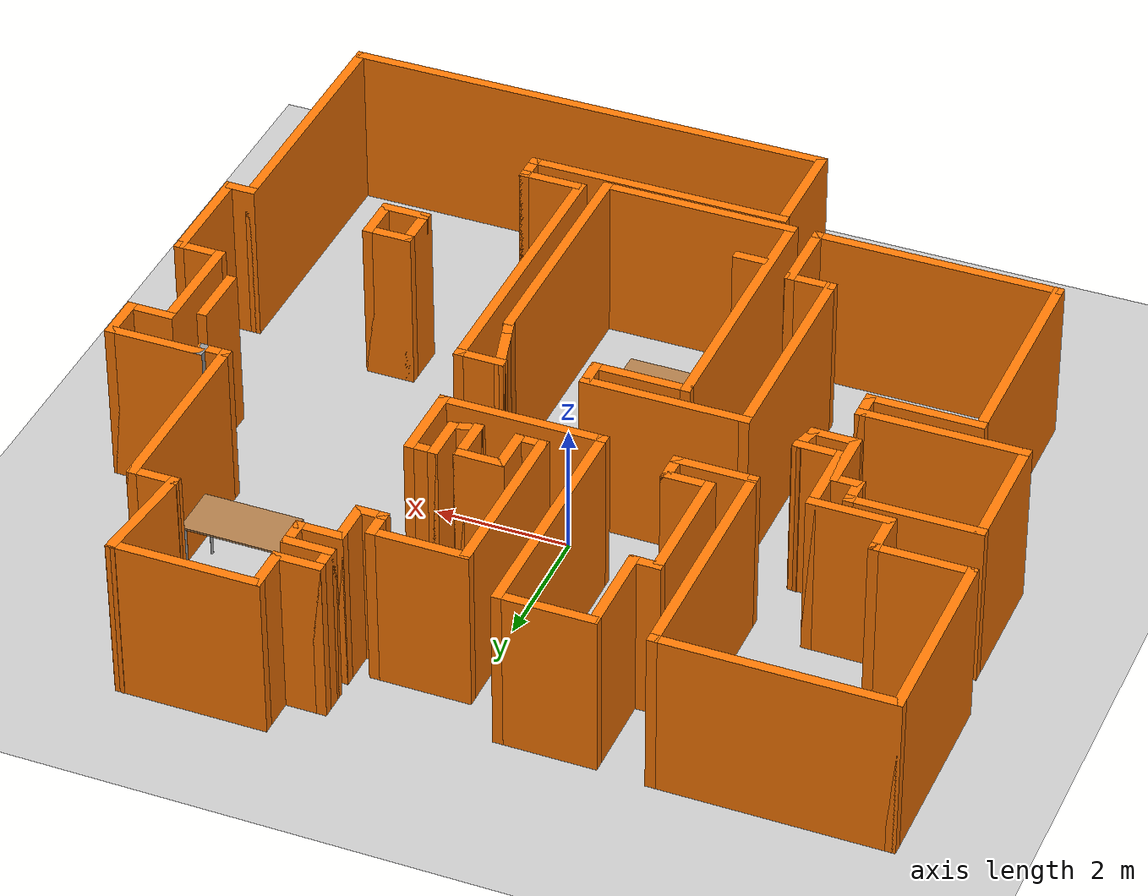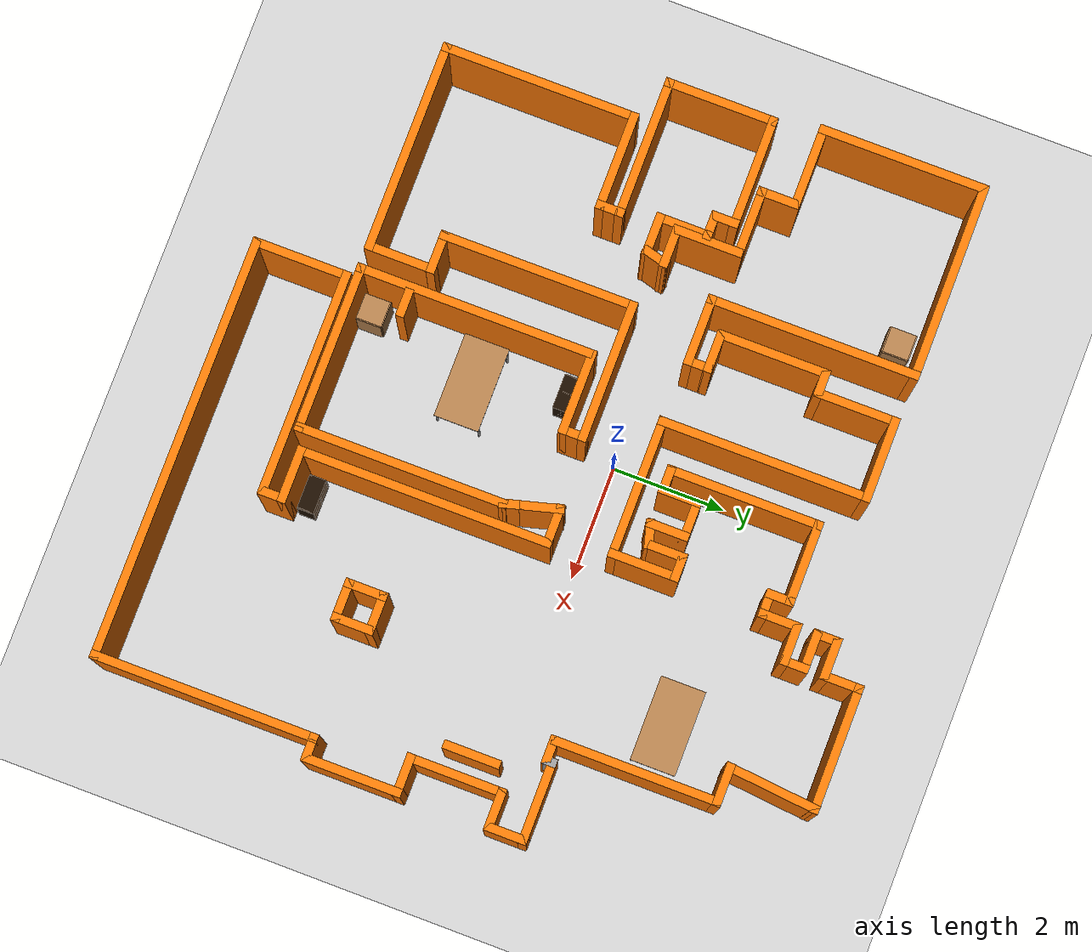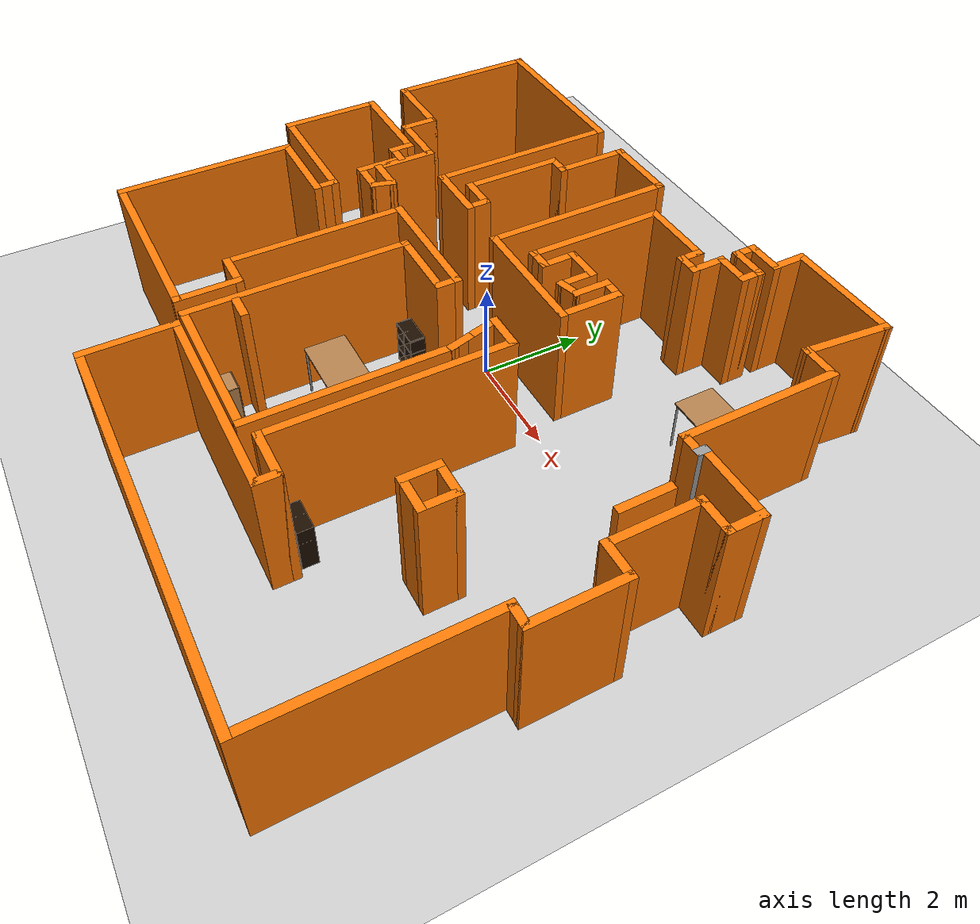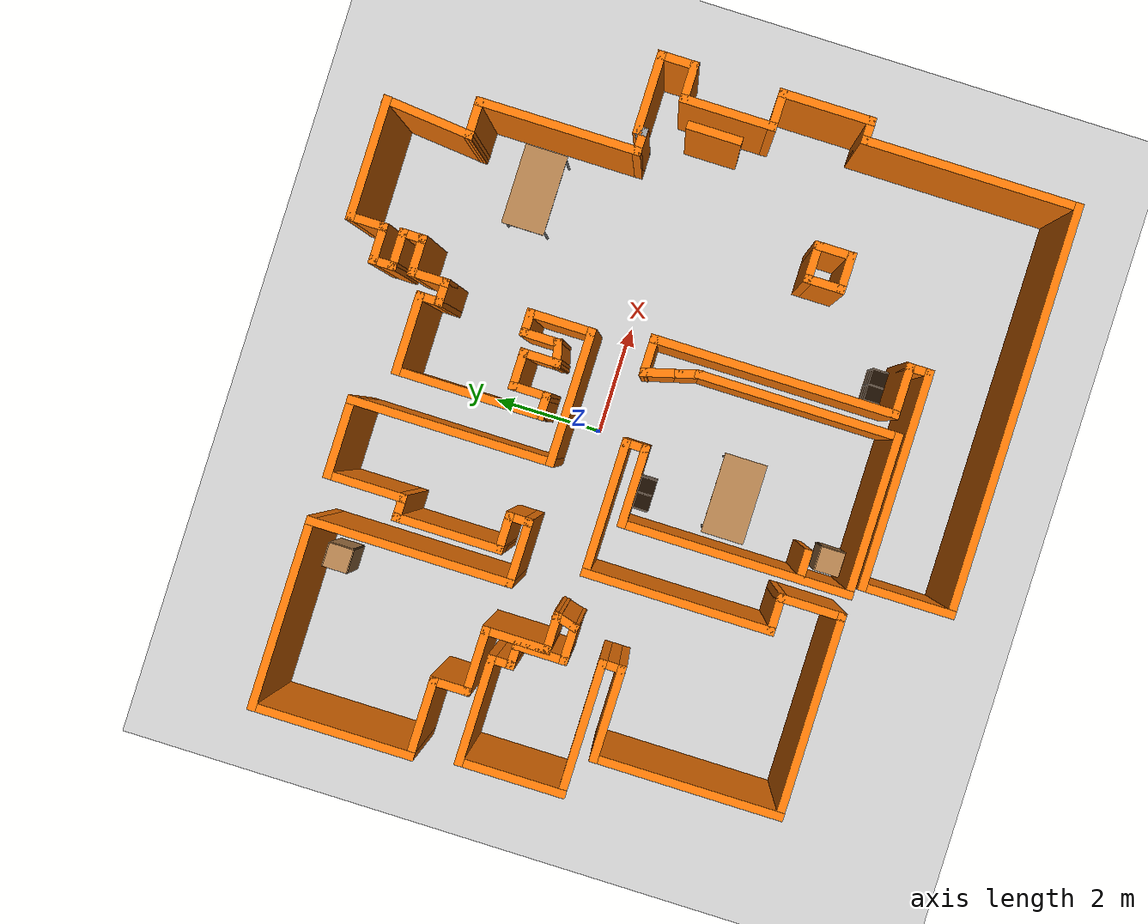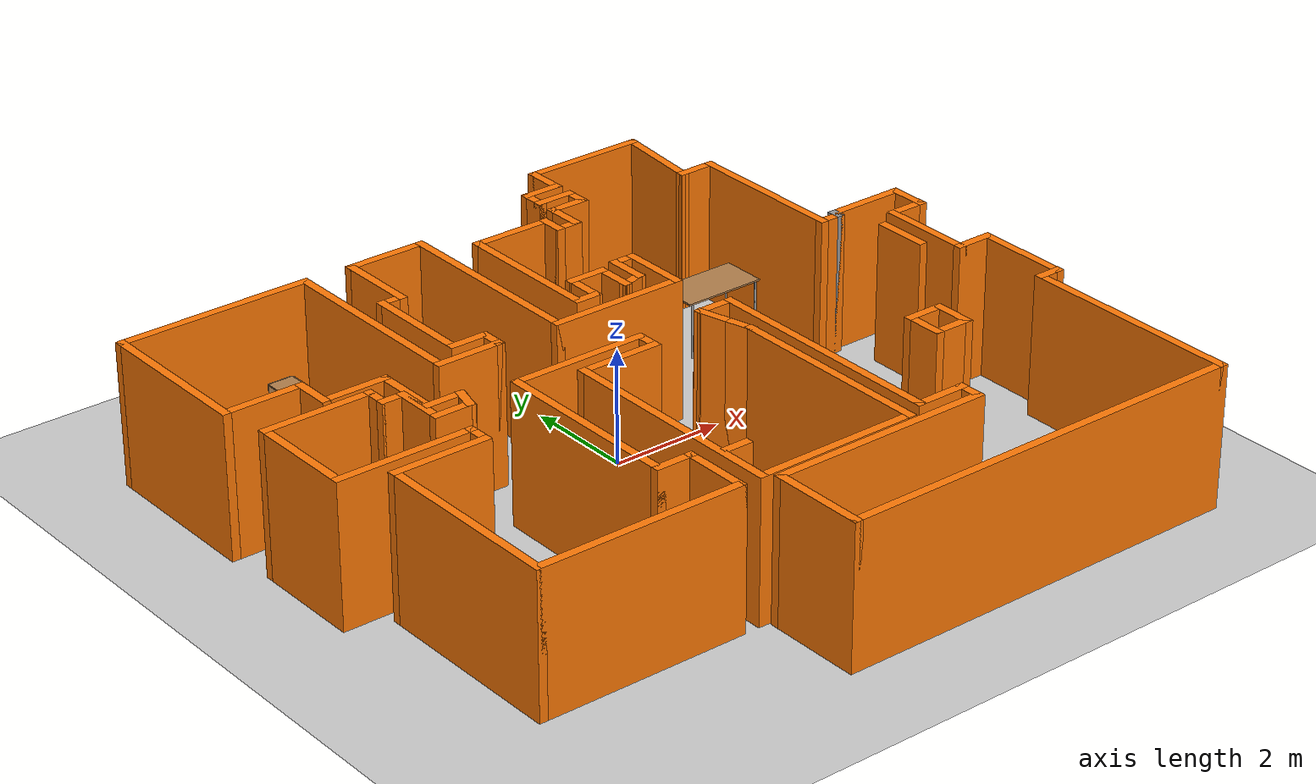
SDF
<sdf version="1.6">
 <world name="default">
  <light name="sun" type="directional">
   <pose>0 0 10 0 -0 0</pose>
   <diffuse>0.8 0.8 0.8 1</diffuse>
   <specular>0.2 0.2 0.2 1</specular>
   <attenuation>
    <range>1000</range>
    <constant>0.9</constant>
    <linear>0.01</linear>
    <quadratic>0.001</quadratic>
   </attenuation>
   <direction>-0.5 0.1 -0.9</direction>
  </light>
  <model name="ground_plane">
   <static>1</static>
   <link name="link">
    <collision name="collision">
     <geometry><plane><normal>0 0 1</normal><size>100 100</size></plane></geometry>
     <surface>
      <contact><collide_bitmask>65535</collide_bitmask></contact>
      <friction><ode><mu>100</mu><mu2>50</mu2></ode></friction>
     </surface>
    </collision>
    <visual name="visual">
     <cast_shadows>0</cast_shadows>
     <geometry><plane><normal>0 0 1</normal><size>100 100</size></plane></geometry>
     <material>
      <script><uri>file://media/materials/scripts/gazebo.material</uri><name>Gazebo/Grey</name></script>
     </material>
    </visual>
   </link>
  </model>
  <gravity>0 0 -9.8</gravity>
  <magnetic_field>6e-06 2.3e-05 -4.2e-05</magnetic_field>
  <atmosphere type="adiabatic"/>
  <physics name="default_physics" default="0" type="ode">
   <max_step_size>0.001</max_step_size>
   <real_time_factor>1</real_time_factor>
   <real_time_update_rate>1000</real_time_update_rate>
  </physics>
  <scene><ambient>0.4 0.4 0.4 1</ambient><background>0.7 0.7 0.7 1</background><shadows>1</shadows></scene>
  <audio><device>default</device></audio>
  <spherical_coordinates>
   <surface_model>EARTH_WGS84</surface_model>
   <latitude_deg>0</latitude_deg>
   <longitude_deg>0</longitude_deg>
   <elevation>0</elevation>
   <heading_deg>0</heading_deg>
  </spherical_coordinates>
  <model name="map_53">
   <pose>0.130645 -0.848309 0 0 -0 0</pose>
   <link name="Wall_0">
    <collision name="Wall_0_Collision">
     <geometry><box><size>2.25 0.15 2.5</size></box></geometry>
     <pose>0 0 1.25 0 -0 0</pose>
    </collision>
    <visual name="Wall_0_Visual">
     <pose>0 0 1.25 0 -0 0</pose>
     <geometry><box><size>2.25 0.15 2.5</size></box></geometry>
     <material>
      <script><uri>file://media/materials/scripts/gazebo.material</uri><name>Gazebo/Grey</name></script>
      <ambient>0.996078 0.47451 0.0196078 1</ambient>
     </material>
     <meta><layer>0</layer></meta>
    </visual>
    <pose>3.20516 5.96148 0 0 -0 3.14159</pose>
   </link>
   <link name="Wall_1">
    <collision name="Wall_1_Collision">
     <geometry><box><size>0.75 0.15 2.5</size></box></geometry>
     <pose>0 0 1.25 0 -0 0</pose>
    </collision>
    <visual name="Wall_1_Visual">
     <pose>0 0 1.25 0 -0 0</pose>
     <geometry><box><size>0.75 0.15 2.5</size></box></geometry>
     <material>
      <script><uri>file://media/materials/scripts/gazebo.material</uri><name>Gazebo/Grey</name></script>
      <ambient>0.996078 0.47451 0.0196078 1</ambient>
     </material>
     <meta><layer>0</layer></meta>
    </visual>
    <pose>2.15516 5.66148 0 0 -0 -1.5708</pose>
   </link>
   <link name="Wall_10">
    <collision name="Wall_10_Collision">
     <geometry><box><size>1.5 0.15 2.5</size></box></geometry>
     <pose>0 0 1.25 0 -0 0</pose>
    </collision>
    <visual name="Wall_10_Visual">
     <pose>0 0 1.25 0 -0 0</pose>
     <geometry><box><size>1.5 0.15 2.5</size></box></geometry>
     <material>
      <script><uri>file://media/materials/scripts/gazebo.material</uri><name>Gazebo/Grey</name></script>
      <ambient>0.996078 0.47451 0.0196078 1</ambient>
     </material>
     <meta><layer>0</layer></meta>
    </visual>
    <pose>0.530158 4.41148 0 0 -0 3.14159</pose>
   </link>
   <link name="Wall_100">
    <collision name="Wall_100_Collision">
     <geometry><box><size>0.75 0.15 2.5</size></box></geometry>
     <pose>0 0 1.25 0 -0 0</pose>
    </collision>
    <visual name="Wall_100_Visual">
     <pose>0 0 1.25 0 -0 0</pose>
     <geometry><box><size>0.75 0.15 2.5</size></box></geometry>
     <material>
      <script><uri>file://media/materials/scripts/gazebo.material</uri><name>Gazebo/Grey</name></script>
      <ambient>0.996078 0.47451 0.0196078 1</ambient>
     </material>
     <meta><layer>0</layer></meta>
    </visual>
    <pose>4.40677 4.43163 0 0 -0 3.14159</pose>
   </link>
   <link name="Wall_101">
    <collision name="Wall_101_Collision">
     <geometry><box><size>1.68704 0.15 2.5</size></box></geometry>
     <pose>0 0 1.25 0 -0 0</pose>
    </collision>
    <visual name="Wall_101_Visual">
     <pose>0 0 1.25 0 -0 0</pose>
     <geometry><box><size>1.68704 0.15 2.5</size></box></geometry>
     <material>
      <script><uri>file://media/materials/scripts/gazebo.material</uri><name>Gazebo/Grey</name></script>
      <ambient>0.996078 0.47451 0.0196078 1</ambient>
     </material>
     <meta><layer>0</layer></meta>
    </visual>
    <pose>4.18096 5.19656 0 0 -0 1.4741</pose>
   </link>
   <link name="Wall_103">
    <collision name="Wall_103_Collision">
     <geometry><box><size>0.75 0.15 2.5</size></box></geometry>
     <pose>0 0 1.25 0 -0 0</pose>
    </collision>
    <visual name="Wall_103_Visual">
     <pose>0 0 1.25 0 -0 0</pose>
     <geometry><box><size>0.75 0.15 2.5</size></box></geometry>
     <material>
      <script><uri>file://media/materials/scripts/gazebo.material</uri><name>Gazebo/Grey</name></script>
      <ambient>0.996078 0.47451 0.0196078 1</ambient>
     </material>
     <meta><layer>0</layer></meta>
    </visual>
    <pose>3.48375 -2.18558 0 0 -0 -1.5708</pose>
   </link>
   <link name="Wall_104">
    <collision name="Wall_104_Collision">
     <geometry><box><size>0.75 0.15 2.5</size></box></geometry>
     <pose>0 0 1.25 0 -0 0</pose>
    </collision>
    <visual name="Wall_104_Visual">
     <pose>0 0 1.25 0 -0 0</pose>
     <geometry><box><size>0.75 0.15 2.5</size></box></geometry>
     <material>
      <script><uri>file://media/materials/scripts/gazebo.material</uri><name>Gazebo/Grey</name></script>
      <ambient>0.996078 0.47451 0.0196078 1</ambient>
     </material>
     <meta><layer>0</layer></meta>
    </visual>
    <pose>3.78375 -2.48557 0 0 -0 0</pose>
   </link>
   <link name="Wall_105">
    <collision name="Wall_105_Collision">
     <geometry><box><size>0.75 0.15 2.5</size></box></geometry>
     <pose>0 0 1.25 0 -0 0</pose>
    </collision>
    <visual name="Wall_105_Visual">
     <pose>0 0 1.25 0 -0 0</pose>
     <geometry><box><size>0.75 0.15 2.5</size></box></geometry>
     <material>
      <script><uri>file://media/materials/scripts/gazebo.material</uri><name>Gazebo/Grey</name></script>
      <ambient>0.996078 0.47451 0.0196078 1</ambient>
     </material>
     <meta><layer>0</layer></meta>
    </visual>
    <pose>4.08375 -2.18558 0 0 -0 1.5708</pose>
   </link>
   <link name="Wall_106">
    <collision name="Wall_106_Collision">
     <geometry><box><size>0.75 0.15 2.5</size></box></geometry>
     <pose>0 0 1.25 0 -0 0</pose>
    </collision>
    <visual name="Wall_106_Visual">
     <pose>0 0 1.25 0 -0 0</pose>
     <geometry><box><size>0.75 0.15 2.5</size></box></geometry>
     <material>
      <script><uri>file://media/materials/scripts/gazebo.material</uri><name>Gazebo/Grey</name></script>
      <ambient>0.996078 0.47451 0.0196078 1</ambient>
     </material>
     <meta><layer>0</layer></meta>
    </visual>
    <pose>3.78375 -1.88558 0 0 -0 3.14159</pose>
   </link>
   <link name="Wall_108">
    <collision name="Wall_108_Collision">
     <geometry><box><size>1 0.15 2.5</size></box></geometry>
     <pose>0 0 1.25 0 -0 0</pose>
    </collision>
    <visual name="Wall_108_Visual">
     <pose>0 0 1.25 0 -0 0</pose>
     <geometry><box><size>1 0.15 2.5</size></box></geometry>
     <material>
      <script><uri>file://media/materials/scripts/gazebo.material</uri><name>Gazebo/Grey</name></script>
      <ambient>0.996078 0.47451 0.0196078 1</ambient>
     </material>
     <meta><layer>0</layer></meta>
    </visual>
    <pose>5.39897 0.402645 0 0 -0 -1.5708</pose>
   </link>
   <link name="Wall_110">
    <collision name="Wall_110_Collision">
     <geometry><box><size>0.5 0.15 2.5</size></box></geometry>
     <pose>0 0 1.25 0 -0 0</pose>
    </collision>
    <visual name="Wall_110_Visual">
     <pose>0 0 1.25 0 -0 0</pose>
     <geometry><box><size>0.5 0.15 2.5</size></box></geometry>
     <material>
      <script><uri>file://media/materials/scripts/gazebo.material</uri><name>Gazebo/Grey</name></script>
      <ambient>0.996078 0.47451 0.0196078 1</ambient>
     </material>
     <meta><layer>0</layer></meta>
    </visual>
    <pose>-1.20908 -3.29539 0 0 -0 0</pose>
   </link>
   <link name="Wall_19">
    <collision name="Wall_19_Collision">
     <geometry><box><size>2.75 0.15 2.5</size></box></geometry>
     <pose>0 0 1.25 0 -0 0</pose>
    </collision>
    <visual name="Wall_19_Visual">
     <pose>0 0 1.25 0 -0 0</pose>
     <geometry><box><size>2.75 0.15 2.5</size></box></geometry>
     <material>
      <script><uri>file://media/materials/scripts/gazebo.material</uri><name>Gazebo/Grey</name></script>
      <ambient>0.996078 0.47451 0.0196078 1</ambient>
     </material>
     <meta><layer>0</layer></meta>
    </visual>
    <pose>-0.144842 3.11148 0 0 -0 -1.5708</pose>
   </link>
   <link name="Wall_2">
    <collision name="Wall_2_Collision">
     <geometry><box><size>0.75 0.15 2.5</size></box></geometry>
     <pose>0 0 1.25 0 -0 0</pose>
    </collision>
    <visual name="Wall_2_Visual">
     <pose>0 0 1.25 0 -0 0</pose>
     <geometry><box><size>0.75 0.15 2.5</size></box></geometry>
     <material>
      <script><uri>file://media/materials/scripts/gazebo.material</uri><name>Gazebo/Grey</name></script>
      <ambient>0.996078 0.47451 0.0196078 1</ambient>
     </material>
     <meta><layer>0</layer></meta>
    </visual>
    <pose>1.85516 5.36148 0 0 -0 3.14159</pose>
   </link>
   <link name="Wall_20">
    <collision name="Wall_20_Collision">
     <geometry><box><size>0.5 0.15 2.5</size></box></geometry>
     <pose>0 0 1.25 0 -0 0</pose>
    </collision>
    <visual name="Wall_20_Visual">
     <pose>0 0 1.25 0 -0 0</pose>
     <geometry><box><size>0.5 0.15 2.5</size></box></geometry>
     <material>
      <script><uri>file://media/materials/scripts/gazebo.material</uri><name>Gazebo/Grey</name></script>
      <ambient>0.996078 0.47451 0.0196078 1</ambient>
     </material>
     <meta><layer>0</layer></meta>
    </visual>
    <pose>0.030158 1.81148 0 0 -0 0</pose>
   </link>
   <link name="Wall_21">
    <collision name="Wall_21_Collision">
     <geometry><box><size>0.75 0.15 2.5</size></box></geometry>
     <pose>0 0 1.25 0 -0 0</pose>
    </collision>
    <visual name="Wall_21_Visual">
     <pose>0 0 1.25 0 -0 0</pose>
     <geometry><box><size>0.75 0.15 2.5</size></box></geometry>
     <material>
      <script><uri>file://media/materials/scripts/gazebo.material</uri><name>Gazebo/Grey</name></script>
      <ambient>0.996078 0.47451 0.0196078 1</ambient>
     </material>
     <meta><layer>0</layer></meta>
    </visual>
    <pose>0.205158 2.11148 0 0 -0 1.5708</pose>
   </link>
   <link name="Wall_22">
    <collision name="Wall_22_Collision">
     <geometry><box><size>0.75 0.15 2.5</size></box></geometry>
     <pose>0 0 1.25 0 -0 0</pose>
    </collision>
    <visual name="Wall_22_Visual">
     <pose>0 0 1.25 0 -0 0</pose>
     <geometry><box><size>0.75 0.15 2.5</size></box></geometry>
     <material>
      <script><uri>file://media/materials/scripts/gazebo.material</uri><name>Gazebo/Grey</name></script>
      <ambient>0.996078 0.47451 0.0196078 1</ambient>
     </material>
     <meta><layer>0</layer></meta>
    </visual>
    <pose>0.505158 2.41148 0 0 -0 0</pose>
   </link>
   <link name="Wall_23">
    <collision name="Wall_23_Collision">
     <geometry><box><size>0.75 0.15 2.5</size></box></geometry>
     <pose>0 0 1.25 0 -0 0</pose>
    </collision>
    <visual name="Wall_23_Visual">
     <pose>0 0 1.25 0 -0 0</pose>
     <geometry><box><size>0.75 0.15 2.5</size></box></geometry>
     <material>
      <script><uri>file://media/materials/scripts/gazebo.material</uri><name>Gazebo/Grey</name></script>
      <ambient>0.996078 0.47451 0.0196078 1</ambient>
     </material>
     <meta><layer>0</layer></meta>
    </visual>
    <pose>0.805158 2.11148 0 0 -0 -1.5708</pose>
   </link>
   <link name="Wall_24">
    <collision name="Wall_24_Collision">
     <geometry><box><size>0.5 0.15 2.5</size></box></geometry>
     <pose>0 0 1.25 0 -0 0</pose>
    </collision>
    <visual name="Wall_24_Visual">
     <pose>0 0 1.25 0 -0 0</pose>
     <geometry><box><size>0.5 0.15 2.5</size></box></geometry>
     <material>
      <script><uri>file://media/materials/scripts/gazebo.material</uri><name>Gazebo/Grey</name></script>
      <ambient>0.996078 0.47451 0.0196078 1</ambient>
     </material>
     <meta><layer>0</layer></meta>
    </visual>
    <pose>0.974195 1.85678 0 0 -0 0.261799</pose>
   </link>
   <link name="Wall_27">
    <collision name="Wall_27_Collision">
     <geometry><box><size>0.75 0.15 2.5</size></box></geometry>
     <pose>0 0 1.25 0 -0 0</pose>
    </collision>
    <visual name="Wall_27_Visual">
     <pose>0 0 1.25 0 -0 0</pose>
     <geometry><box><size>0.75 0.15 2.5</size></box></geometry>
     <material>
      <script><uri>file://media/materials/scripts/gazebo.material</uri><name>Gazebo/Grey</name></script>
      <ambient>0.996078 0.47451 0.0196078 1</ambient>
     </material>
     <meta><layer>0</layer></meta>
    </visual>
    <pose>1.14323 2.20207 0 0 -0 1.5708</pose>
   </link>
   <link name="Wall_28">
    <collision name="Wall_28_Collision">
     <geometry><box><size>0.5 0.15 2.5</size></box></geometry>
     <pose>0 0 1.25 0 -0 0</pose>
    </collision>
    <visual name="Wall_28_Visual">
     <pose>0 0 1.25 0 -0 0</pose>
     <geometry><box><size>0.5 0.15 2.5</size></box></geometry>
     <material>
      <script><uri>file://media/materials/scripts/gazebo.material</uri><name>Gazebo/Grey</name></script>
      <ambient>0.996078 0.47451 0.0196078 1</ambient>
     </material>
     <meta><layer>0</layer></meta>
    </visual>
    <pose>1.31823 2.50207 0 0 -0 0</pose>
   </link>
   <link name="Wall_29">
    <collision name="Wall_29_Collision">
     <geometry><box><size>1.25 0.15 2.5</size></box></geometry>
     <pose>0 0 1.25 0 -0 0</pose>
    </collision>
    <visual name="Wall_29_Visual">
     <pose>0 0 1.25 0 -0 0</pose>
     <geometry><box><size>1.25 0.15 2.5</size></box></geometry>
     <material>
      <script><uri>file://media/materials/scripts/gazebo.material</uri><name>Gazebo/Grey</name></script>
      <ambient>0.996078 0.47451 0.0196078 1</ambient>
     </material>
     <meta><layer>0</layer></meta>
    </visual>
    <pose>1.49323 1.95207 0 0 -0 -1.5708</pose>
   </link>
   <link name="Wall_3">
    <collision name="Wall_3_Collision">
     <geometry><box><size>0.5 0.15 2.5</size></box></geometry>
     <pose>0 0 1.25 0 -0 0</pose>
    </collision>
    <visual name="Wall_3_Visual">
     <pose>0 0 1.25 0 -0 0</pose>
     <geometry><box><size>0.5 0.15 2.5</size></box></geometry>
     <material>
      <script><uri>file://media/materials/scripts/gazebo.material</uri><name>Gazebo/Grey</name></script>
      <ambient>0.996078 0.47451 0.0196078 1</ambient>
     </material>
     <meta><layer>0</layer></meta>
    </visual>
    <pose>1.55516 5.18648 0 0 -0 -1.5708</pose>
   </link>
   <link name="Wall_30">
    <collision name="Wall_30_Collision">
     <geometry><box><size>2.5 0.15 2.5</size></box></geometry>
     <pose>0 0 1.25 0 -0 0</pose>
    </collision>
    <visual name="Wall_30_Visual">
     <pose>0 0 1.25 0 -0 0</pose>
     <geometry><box><size>2.5 0.15 2.5</size></box></geometry>
     <material>
      <script><uri>file://media/materials/scripts/gazebo.material</uri><name>Gazebo/Grey</name></script>
      <ambient>0.996078 0.47451 0.0196078 1</ambient>
     </material>
     <meta><layer>0</layer></meta>
    </visual>
    <pose>0.318232 1.40207 0 0 -0 3.14159</pose>
   </link>
   <link name="Wall_31">
    <collision name="Wall_31_Collision">
     <geometry><box><size>3.75 0.15 2.5</size></box></geometry>
     <pose>0 0 1.25 0 -0 0</pose>
    </collision>
    <visual name="Wall_31_Visual">
     <pose>0 0 1.25 0 -0 0</pose>
     <geometry><box><size>3.75 0.15 2.5</size></box></geometry>
     <material>
      <script><uri>file://media/materials/scripts/gazebo.material</uri><name>Gazebo/Grey</name></script>
      <ambient>0.996078 0.47451 0.0196078 1</ambient>
     </material>
     <meta><layer>0</layer></meta>
    </visual>
    <pose>-0.856768 3.20207 0 0 -0 1.5708</pose>
   </link>
   <link name="Wall_32">
    <collision name="Wall_32_Collision">
     <geometry><box><size>1.5 0.15 2.5</size></box></geometry>
     <pose>0 0 1.25 0 -0 0</pose>
    </collision>
    <visual name="Wall_32_Visual">
     <pose>0 0 1.25 0 -0 0</pose>
     <geometry><box><size>1.5 0.15 2.5</size></box></geometry>
     <material>
      <script><uri>file://media/materials/scripts/gazebo.material</uri><name>Gazebo/Grey</name></script>
      <ambient>0.996078 0.47451 0.0196078 1</ambient>
     </material>
     <meta><layer>0</layer></meta>
    </visual>
    <pose>-1.53177 5.00207 0 0 -0 3.14159</pose>
   </link>
   <link name="Wall_39">
    <collision name="Wall_39_Collision">
     <geometry><box><size>1.5 0.15 2.5</size></box></geometry>
     <pose>0 0 1.25 0 -0 0</pose>
    </collision>
    <visual name="Wall_39_Visual">
     <pose>0 0 1.25 0 -0 0</pose>
     <geometry><box><size>1.5 0.15 2.5</size></box></geometry>
     <material>
      <script><uri>file://media/materials/scripts/gazebo.material</uri><name>Gazebo/Grey</name></script>
      <ambient>0.996078 0.47451 0.0196078 1</ambient>
     </material>
     <meta><layer>0</layer></meta>
    </visual>
    <pose>-2.20677 4.32707 0 0 -0 -1.5708</pose>
   </link>
   <link name="Wall_4">
    <collision name="Wall_4_Collision">
     <geometry><box><size>0.75 0.15 2.5</size></box></geometry>
     <pose>0 0 1.25 0 -0 0</pose>
    </collision>
    <visual name="Wall_4_Visual">
     <pose>0 0 1.25 0 -0 0</pose>
     <geometry><box><size>0.75 0.15 2.5</size></box></geometry>
     <material>
      <script><uri>file://media/materials/scripts/gazebo.material</uri><name>Gazebo/Grey</name></script>
      <ambient>0.996078 0.47451 0.0196078 1</ambient>
     </material>
     <meta><layer>0</layer></meta>
    </visual>
    <pose>1.85516 5.01148 0 0 -0 0</pose>
   </link>
   <link name="Wall_40">
    <collision name="Wall_40_Collision">
     <geometry><box><size>0.5 0.15 2.5</size></box></geometry>
     <pose>0 0 1.25 0 -0 0</pose>
    </collision>
    <visual name="Wall_40_Visual">
     <pose>0 0 1.25 0 -0 0</pose>
     <geometry><box><size>0.5 0.15 2.5</size></box></geometry>
     <material>
      <script><uri>file://media/materials/scripts/gazebo.material</uri><name>Gazebo/Grey</name></script>
      <ambient>0.996078 0.47451 0.0196078 1</ambient>
     </material>
     <meta><layer>0</layer></meta>
    </visual>
    <pose>-2.38177 3.65207 0 0 -0 3.14159</pose>
   </link>
   <link name="Wall_41">
    <collision name="Wall_41_Collision">
     <geometry><box><size>2 0.15 2.5</size></box></geometry>
     <pose>0 0 1.25 0 -0 0</pose>
    </collision>
    <visual name="Wall_41_Visual">
     <pose>0 0 1.25 0 -0 0</pose>
     <geometry><box><size>2 0.15 2.5</size></box></geometry>
     <material>
      <script><uri>file://media/materials/scripts/gazebo.material</uri><name>Gazebo/Grey</name></script>
      <ambient>0.996078 0.47451 0.0196078 1</ambient>
     </material>
     <meta><layer>0</layer></meta>
    </visual>
    <pose>-2.55677 2.72707 0 0 -0 -1.5708</pose>
   </link>
   <link name="Wall_42">
    <collision name="Wall_42_Collision">
     <geometry><box><size>0.75 0.15 2.5</size></box></geometry>
     <pose>0 0 1.25 0 -0 0</pose>
    </collision>
    <visual name="Wall_42_Visual">
     <pose>0 0 1.25 0 -0 0</pose>
     <geometry><box><size>0.75 0.15 2.5</size></box></geometry>
     <material>
      <script><uri>file://media/materials/scripts/gazebo.material</uri><name>Gazebo/Grey</name></script>
      <ambient>0.996078 0.47451 0.0196078 1</ambient>
     </material>
     <meta><layer>0</layer></meta>
    </visual>
    <pose>-2.25677 1.80207 0 0 -0 0</pose>
   </link>
   <link name="Wall_43">
    <collision name="Wall_43_Collision">
     <geometry><box><size>0.5 0.15 2.5</size></box></geometry>
     <pose>0 0 1.25 0 -0 0</pose>
    </collision>
    <visual name="Wall_43_Visual">
     <pose>0 0 1.25 0 -0 0</pose>
     <geometry><box><size>0.5 0.15 2.5</size></box></geometry>
     <material>
      <script><uri>file://media/materials/scripts/gazebo.material</uri><name>Gazebo/Grey</name></script>
      <ambient>0.996078 0.47451 0.0196078 1</ambient>
     </material>
     <meta><layer>0</layer></meta>
    </visual>
    <pose>-1.95677 1.62707 0 0 -0 -1.5708</pose>
   </link>
   <link name="Wall_44">
    <collision name="Wall_44_Collision">
     <geometry><box><size>1.25 0.15 2.5</size></box></geometry>
     <pose>0 0 1.25 0 -0 0</pose>
    </collision>
    <visual name="Wall_44_Visual">
     <pose>0 0 1.25 0 -0 0</pose>
     <geometry><box><size>1.25 0.15 2.5</size></box></geometry>
     <material>
      <script><uri>file://media/materials/scripts/gazebo.material</uri><name>Gazebo/Grey</name></script>
      <ambient>0.996078 0.47451 0.0196078 1</ambient>
     </material>
     <meta><layer>0</layer></meta>
    </visual>
    <pose>-2.50677 1.45207 0 0 -0 3.14159</pose>
   </link>
   <link name="Wall_45">
    <collision name="Wall_45_Collision">
     <geometry><box><size>3.75 0.15 2.5</size></box></geometry>
     <pose>0 0 1.25 0 -0 0</pose>
    </collision>
    <visual name="Wall_45_Visual">
     <pose>0 0 1.25 0 -0 0</pose>
     <geometry><box><size>3.75 0.15 2.5</size></box></geometry>
     <material>
      <script><uri>file://media/materials/scripts/gazebo.material</uri><name>Gazebo/Grey</name></script>
      <ambient>0.996078 0.47451 0.0196078 1</ambient>
     </material>
     <meta><layer>0</layer></meta>
    </visual>
    <pose>-3.05677 3.25207 0 0 -0 1.5708</pose>
   </link>
   <link name="Wall_46">
    <collision name="Wall_46_Collision">
     <geometry><box><size>3.5 0.15 2.5</size></box></geometry>
     <pose>0 0 1.25 0 -0 0</pose>
    </collision>
    <visual name="Wall_46_Visual">
     <pose>0 0 1.25 0 -0 0</pose>
     <geometry><box><size>3.5 0.15 2.5</size></box></geometry>
     <material>
      <script><uri>file://media/materials/scripts/gazebo.material</uri><name>Gazebo/Grey</name></script>
      <ambient>0.996078 0.47451 0.0196078 1</ambient>
     </material>
     <meta><layer>0</layer></meta>
    </visual>
    <pose>-4.73177 5.05207 0 0 -0 3.14159</pose>
   </link>
   <link name="Wall_47">
    <collision name="Wall_47_Collision">
     <geometry><box><size>3 0.15 2.5</size></box></geometry>
     <pose>0 0 1.25 0 -0 0</pose>
    </collision>
    <visual name="Wall_47_Visual">
     <pose>0 0 1.25 0 -0 0</pose>
     <geometry><box><size>3 0.15 2.5</size></box></geometry>
     <material>
      <script><uri>file://media/materials/scripts/gazebo.material</uri><name>Gazebo/Grey</name></script>
      <ambient>0.996078 0.47451 0.0196078 1</ambient>
     </material>
     <meta><layer>0</layer></meta>
    </visual>
    <pose>-6.40677 3.62707 0 0 -0 -1.5708</pose>
   </link>
   <link name="Wall_48">
    <collision name="Wall_48_Collision">
     <geometry><box><size>1.5 0.15 2.5</size></box></geometry>
     <pose>0 0 1.25 0 -0 0</pose>
    </collision>
    <visual name="Wall_48_Visual">
     <pose>0 0 1.25 0 -0 0</pose>
     <geometry><box><size>1.5 0.15 2.5</size></box></geometry>
     <material>
      <script><uri>file://media/materials/scripts/gazebo.material</uri><name>Gazebo/Grey</name></script>
      <ambient>0.996078 0.47451 0.0196078 1</ambient>
     </material>
     <meta><layer>0</layer></meta>
    </visual>
    <pose>-5.73177 2.20207 0 0 -0 0</pose>
   </link>
   <link name="Wall_49">
    <collision name="Wall_49_Collision">
     <geometry><box><size>0.75 0.15 2.5</size></box></geometry>
     <pose>0 0 1.25 0 -0 0</pose>
    </collision>
    <visual name="Wall_49_Visual">
     <pose>0 0 1.25 0 -0 0</pose>
     <geometry><box><size>0.75 0.15 2.5</size></box></geometry>
     <material>
      <script><uri>file://media/materials/scripts/gazebo.material</uri><name>Gazebo/Grey</name></script>
      <ambient>0.996078 0.47451 0.0196078 1</ambient>
     </material>
     <meta><layer>0</layer></meta>
    </visual>
    <pose>-5.05677 1.90207 0 0 -0 -1.5708</pose>
   </link>
   <link name="Wall_5">
    <collision name="Wall_5_Collision">
     <geometry><box><size>0.5 0.15 2.5</size></box></geometry>
     <pose>0 0 1.25 0 -0 0</pose>
    </collision>
    <visual name="Wall_5_Visual">
     <pose>0 0 1.25 0 -0 0</pose>
     <geometry><box><size>0.5 0.15 2.5</size></box></geometry>
     <material>
      <script><uri>file://media/materials/scripts/gazebo.material</uri><name>Gazebo/Grey</name></script>
      <ambient>0.996078 0.47451 0.0196078 1</ambient>
     </material>
     <meta><layer>0</layer></meta>
    </visual>
    <pose>2.15516 4.83648 0 0 -0 -1.5708</pose>
   </link>
   <link name="Wall_50">
    <collision name="Wall_50_Collision">
     <geometry><box><size>1.25 0.15 2.5</size></box></geometry>
     <pose>0 0 1.25 0 -0 0</pose>
    </collision>
    <visual name="Wall_50_Visual">
     <pose>0 0 1.25 0 -0 0</pose>
     <geometry><box><size>1.25 0.15 2.5</size></box></geometry>
     <material>
      <script><uri>file://media/materials/scripts/gazebo.material</uri><name>Gazebo/Grey</name></script>
      <ambient>0.996078 0.47451 0.0196078 1</ambient>
     </material>
     <meta><layer>0</layer></meta>
    </visual>
    <pose>-4.50677 1.60207 0 0 -0 0</pose>
   </link>
   <link name="Wall_51">
    <collision name="Wall_51_Collision">
     <geometry><box><size>1.25 0.15 2.5</size></box></geometry>
     <pose>0 0 1.25 0 -0 0</pose>
    </collision>
    <visual name="Wall_51_Visual">
     <pose>0 0 1.25 0 -0 0</pose>
     <geometry><box><size>1.25 0.15 2.5</size></box></geometry>
     <material>
      <script><uri>file://media/materials/scripts/gazebo.material</uri><name>Gazebo/Grey</name></script>
      <ambient>0.996078 0.47451 0.0196078 1</ambient>
     </material>
     <meta><layer>0</layer></meta>
    </visual>
    <pose>-3.95677 1.05207 0 0 -0 -1.5708</pose>
   </link>
   <link name="Wall_52">
    <collision name="Wall_52_Collision">
     <geometry><box><size>0.75 0.15 2.5</size></box></geometry>
     <pose>0 0 1.25 0 -0 0</pose>
    </collision>
    <visual name="Wall_52_Visual">
     <pose>0 0 1.25 0 -0 0</pose>
     <geometry><box><size>0.75 0.15 2.5</size></box></geometry>
     <material>
      <script><uri>file://media/materials/scripts/gazebo.material</uri><name>Gazebo/Grey</name></script>
      <ambient>0.996078 0.47451 0.0196078 1</ambient>
     </material>
     <meta><layer>0</layer></meta>
    </visual>
    <pose>-3.65677 0.50207 0 0 -0 0</pose>
   </link>
   <link name="Wall_53">
    <collision name="Wall_53_Collision">
     <geometry><box><size>0.5 0.15 2.5</size></box></geometry>
     <pose>0 0 1.25 0 -0 0</pose>
    </collision>
    <visual name="Wall_53_Visual">
     <pose>0 0 1.25 0 -0 0</pose>
     <geometry><box><size>0.5 0.15 2.5</size></box></geometry>
     <material>
      <script><uri>file://media/materials/scripts/gazebo.material</uri><name>Gazebo/Grey</name></script>
      <ambient>0.996078 0.47451 0.0196078 1</ambient>
     </material>
     <meta><layer>0</layer></meta>
    </visual>
    <pose>-3.40206 0.333033 0 0 -0 -1.8326</pose>
   </link>
   <link name="Wall_54">
    <collision name="Wall_54_Collision">
     <geometry><box><size>0.75 0.15 2.5</size></box></geometry>
     <pose>0 0 1.25 0 -0 0</pose>
    </collision>
    <visual name="Wall_54_Visual">
     <pose>0 0 1.25 0 -0 0</pose>
     <geometry><box><size>0.75 0.15 2.5</size></box></geometry>
     <material>
      <script><uri>file://media/materials/scripts/gazebo.material</uri><name>Gazebo/Grey</name></script>
      <ambient>0.996078 0.47451 0.0196078 1</ambient>
     </material>
     <meta><layer>0</layer></meta>
    </visual>
    <pose>-3.74735 0.163996 0 0 -0 3.14159</pose>
   </link>
   <link name="Wall_55">
    <collision name="Wall_55_Collision">
     <geometry><box><size>1 0.15 2.5</size></box></geometry>
     <pose>0 0 1.25 0 -0 0</pose>
    </collision>
    <visual name="Wall_55_Visual">
     <pose>0 0 1.25 0 -0 0</pose>
     <geometry><box><size>1 0.15 2.5</size></box></geometry>
     <material>
      <script><uri>file://media/materials/scripts/gazebo.material</uri><name>Gazebo/Grey</name></script>
      <ambient>0.996078 0.47451 0.0196078 1</ambient>
     </material>
     <meta><layer>0</layer></meta>
    </visual>
    <pose>-4.04735 0.588996 0 0 -0 1.5708</pose>
   </link>
   <link name="Wall_56">
    <collision name="Wall_56_Collision">
     <geometry><box><size>0.5 0.15 2.5</size></box></geometry>
     <pose>0 0 1.25 0 -0 0</pose>
    </collision>
    <visual name="Wall_56_Visual">
     <pose>0 0 1.25 0 -0 0</pose>
     <geometry><box><size>0.5 0.15 2.5</size></box></geometry>
     <material>
      <script><uri>file://media/materials/scripts/gazebo.material</uri><name>Gazebo/Grey</name></script>
      <ambient>0.996078 0.47451 0.0196078 1</ambient>
     </material>
     <meta><layer>0</layer></meta>
    </visual>
    <pose>-4.22236 1.014 0 0 -0 3.14159</pose>
   </link>
   <link name="Wall_57">
    <collision name="Wall_57_Collision">
     <geometry><box><size>0.5 0.15 2.5</size></box></geometry>
     <pose>0 0 1.25 0 -0 0</pose>
    </collision>
    <visual name="Wall_57_Visual">
     <pose>0 0 1.25 0 -0 0</pose>
     <geometry><box><size>0.5 0.15 2.5</size></box></geometry>
     <material>
      <script><uri>file://media/materials/scripts/gazebo.material</uri><name>Gazebo/Grey</name></script>
      <ambient>0.996078 0.47451 0.0196078 1</ambient>
     </material>
     <meta><layer>0</layer></meta>
    </visual>
    <pose>-4.39736 1.189 0 0 -0 1.5708</pose>
   </link>
   <link name="Wall_58">
    <collision name="Wall_58_Collision">
     <geometry><box><size>2 0.15 2.5</size></box></geometry>
     <pose>0 0 1.25 0 -0 0</pose>
    </collision>
    <visual name="Wall_58_Visual">
     <pose>0 0 1.25 0 -0 0</pose>
     <geometry><box><size>2 0.15 2.5</size></box></geometry>
     <material>
      <script><uri>file://media/materials/scripts/gazebo.material</uri><name>Gazebo/Grey</name></script>
      <ambient>0.996078 0.47451 0.0196078 1</ambient>
     </material>
     <meta><layer>0</layer></meta>
    </visual>
    <pose>-5.32235 1.364 0 0 -0 3.14159</pose>
   </link>
   <link name="Wall_59">
    <collision name="Wall_59_Collision">
     <geometry><box><size>2 0.15 2.5</size></box></geometry>
     <pose>0 0 1.25 0 -0 0</pose>
    </collision>
    <visual name="Wall_59_Visual">
     <pose>0 0 1.25 0 -0 0</pose>
     <geometry><box><size>2 0.15 2.5</size></box></geometry>
     <material>
      <script><uri>file://media/materials/scripts/gazebo.material</uri><name>Gazebo/Grey</name></script>
      <ambient>0.996078 0.47451 0.0196078 1</ambient>
     </material>
     <meta><layer>0</layer></meta>
    </visual>
    <pose>-6.24735 0.438996 0 0 -0 -1.5708</pose>
   </link>
   <link name="Wall_6">
    <collision name="Wall_6_Collision">
     <geometry><box><size>0.75 0.15 2.5</size></box></geometry>
     <pose>0 0 1.25 0 -0 0</pose>
    </collision>
    <visual name="Wall_6_Visual">
     <pose>0 0 1.25 0 -0 0</pose>
     <geometry><box><size>0.75 0.15 2.5</size></box></geometry>
     <material>
      <script><uri>file://media/materials/scripts/gazebo.material</uri><name>Gazebo/Grey</name></script>
      <ambient>0.996078 0.47451 0.0196078 1</ambient>
     </material>
     <meta><layer>0</layer></meta>
    </visual>
    <pose>1.85516 4.66148 0 0 -0 3.14159</pose>
   </link>
   <link name="Wall_60">
    <collision name="Wall_60_Collision">
     <geometry><box><size>2.5 0.15 2.5</size></box></geometry>
     <pose>0 0 1.25 0 -0 0</pose>
    </collision>
    <visual name="Wall_60_Visual">
     <pose>0 0 1.25 0 -0 0</pose>
     <geometry><box><size>2.5 0.15 2.5</size></box></geometry>
     <material>
      <script><uri>file://media/materials/scripts/gazebo.material</uri><name>Gazebo/Grey</name></script>
      <ambient>0.996078 0.47451 0.0196078 1</ambient>
     </material>
     <meta><layer>0</layer></meta>
    </visual>
    <pose>-5.07235 -0.486004 0 0 -0 0</pose>
   </link>
   <link name="Wall_61">
    <collision name="Wall_61_Collision">
     <geometry><box><size>0.5 0.15 2.5</size></box></geometry>
     <pose>0 0 1.25 0 -0 0</pose>
    </collision>
    <visual name="Wall_61_Visual">
     <pose>0 0 1.25 0 -0 0</pose>
     <geometry><box><size>0.5 0.15 2.5</size></box></geometry>
     <material>
      <script><uri>file://media/materials/scripts/gazebo.material</uri><name>Gazebo/Grey</name></script>
      <ambient>0.996078 0.47451 0.0196078 1</ambient>
     </material>
     <meta><layer>0</layer></meta>
    </visual>
    <pose>-3.89736 -0.661004 0 0 -0 -1.5708</pose>
   </link>
   <link name="Wall_62">
    <collision name="Wall_62_Collision">
     <geometry><box><size>1.75 0.15 2.5</size></box></geometry>
     <pose>0 0 1.25 0 -0 0</pose>
    </collision>
    <visual name="Wall_62_Visual">
     <pose>0 0 1.25 0 -0 0</pose>
     <geometry><box><size>1.75 0.15 2.5</size></box></geometry>
     <material>
      <script><uri>file://media/materials/scripts/gazebo.material</uri><name>Gazebo/Grey</name></script>
      <ambient>0.996078 0.47451 0.0196078 1</ambient>
     </material>
     <meta><layer>0</layer></meta>
    </visual>
    <pose>-4.69735 -0.836004 0 0 -0 3.14159</pose>
   </link>
   <link name="Wall_63">
    <collision name="Wall_63_Collision">
     <geometry><box><size>3.5 0.15 2.5</size></box></geometry>
     <pose>0 0 1.25 0 -0 0</pose>
    </collision>
    <visual name="Wall_63_Visual">
     <pose>0 0 1.25 0 -0 0</pose>
     <geometry><box><size>3.5 0.15 2.5</size></box></geometry>
     <material>
      <script><uri>file://media/materials/scripts/gazebo.material</uri><name>Gazebo/Grey</name></script>
      <ambient>0.996078 0.47451 0.0196078 1</ambient>
     </material>
     <meta><layer>0</layer></meta>
    </visual>
    <pose>-5.49735 -2.511 0 0 -0 -1.5708</pose>
   </link>
   <link name="Wall_64">
    <collision name="Wall_64_Collision">
     <geometry><box><size>3.75 0.15 2.5</size></box></geometry>
     <pose>0 0 1.25 0 -0 0</pose>
    </collision>
    <visual name="Wall_64_Visual">
     <pose>0 0 1.25 0 -0 0</pose>
     <geometry><box><size>3.75 0.15 2.5</size></box></geometry>
     <material>
      <script><uri>file://media/materials/scripts/gazebo.material</uri><name>Gazebo/Grey</name></script>
      <ambient>0.996078 0.47451 0.0196078 1</ambient>
     </material>
     <meta><layer>0</layer></meta>
    </visual>
    <pose>-3.69735 -4.186 0 0 -0 0</pose>
   </link>
   <link name="Wall_65">
    <collision name="Wall_65_Collision">
     <geometry><box><size>1.25 0.15 2.5</size></box></geometry>
     <pose>0 0 1.25 0 -0 0</pose>
    </collision>
    <visual name="Wall_65_Visual">
     <pose>0 0 1.25 0 -0 0</pose>
     <geometry><box><size>1.25 0.15 2.5</size></box></geometry>
     <material>
      <script><uri>file://media/materials/scripts/gazebo.material</uri><name>Gazebo/Grey</name></script>
      <ambient>0.996078 0.47451 0.0196078 1</ambient>
     </material>
     <meta><layer>0</layer></meta>
    </visual>
    <pose>-1.89735 -3.636 0 0 -0 1.5708</pose>
   </link>
   <link name="Wall_66">
    <collision name="Wall_66_Collision">
     <geometry><box><size>0.75 0.15 2.5</size></box></geometry>
     <pose>0 0 1.25 0 -0 0</pose>
    </collision>
    <visual name="Wall_66_Visual">
     <pose>0 0 1.25 0 -0 0</pose>
     <geometry><box><size>0.75 0.15 2.5</size></box></geometry>
     <material>
      <script><uri>file://media/materials/scripts/gazebo.material</uri><name>Gazebo/Grey</name></script>
      <ambient>0.996078 0.47451 0.0196078 1</ambient>
     </material>
     <meta><layer>0</layer></meta>
    </visual>
    <pose>-2.19735 -3.086 0 0 -0 3.14159</pose>
   </link>
   <link name="Wall_67">
    <collision name="Wall_67_Collision">
     <geometry><box><size>3.5 0.15 2.5</size></box></geometry>
     <pose>0 0 1.25 0 -0 0</pose>
    </collision>
    <visual name="Wall_67_Visual">
     <pose>0 0 1.25 0 -0 0</pose>
     <geometry><box><size>3.5 0.15 2.5</size></box></geometry>
     <material>
      <script><uri>file://media/materials/scripts/gazebo.material</uri><name>Gazebo/Grey</name></script>
      <ambient>0.996078 0.47451 0.0196078 1</ambient>
     </material>
     <meta><layer>0</layer></meta>
    </visual>
    <pose>-2.49735 -1.411 0 0 -0 1.5708</pose>
   </link>
   <link name="Wall_7">
    <collision name="Wall_7_Collision">
     <geometry><box><size>0.75 0.15 2.5</size></box></geometry>
     <pose>0 0 1.25 0 -0 0</pose>
    </collision>
    <visual name="Wall_7_Visual">
     <pose>0 0 1.25 0 -0 0</pose>
     <geometry><box><size>0.75 0.15 2.5</size></box></geometry>
     <material>
      <script><uri>file://media/materials/scripts/gazebo.material</uri><name>Gazebo/Grey</name></script>
      <ambient>0.996078 0.47451 0.0196078 1</ambient>
     </material>
     <meta><layer>0</layer></meta>
    </visual>
    <pose>1.55516 4.36148 0 0 -0 -1.5708</pose>
   </link>
   <link name="Wall_72">
    <collision name="Wall_72_Collision">
     <geometry><box><size>2.5 0.15 2.5</size></box></geometry>
     <pose>0 0 1.25 0 -0 0</pose>
    </collision>
    <visual name="Wall_72_Visual">
     <pose>0 0 1.25 0 -0 0</pose>
     <geometry><box><size>2.5 0.15 2.5</size></box></geometry>
     <material>
      <script><uri>file://media/materials/scripts/gazebo.material</uri><name>Gazebo/Grey</name></script>
      <ambient>0.996078 0.47451 0.0196078 1</ambient>
     </material>
     <meta><layer>0</layer></meta>
    </visual>
    <pose>-1.32235 0.263996 0 0 -0 0</pose>
   </link>
   <link name="Wall_73">
    <collision name="Wall_73_Collision">
     <geometry><box><size>0.5 0.15 2.5</size></box></geometry>
     <pose>0 0 1.25 0 -0 0</pose>
    </collision>
    <visual name="Wall_73_Visual">
     <pose>0 0 1.25 0 -0 0</pose>
     <geometry><box><size>0.5 0.15 2.5</size></box></geometry>
     <material>
      <script><uri>file://media/materials/scripts/gazebo.material</uri><name>Gazebo/Grey</name></script>
      <ambient>0.996078 0.47451 0.0196078 1</ambient>
     </material>
     <meta><layer>0</layer></meta>
    </visual>
    <pose>-0.147354 0.088996 0 0 -0 -1.5708</pose>
   </link>
   <link name="Wall_74">
    <collision name="Wall_74_Collision">
     <geometry><box><size>1.5 0.15 2.5</size></box></geometry>
     <pose>0 0 1.25 0 -0 0</pose>
    </collision>
    <visual name="Wall_74_Visual">
     <pose>0 0 1.25 0 -0 0</pose>
     <geometry><box><size>1.5 0.15 2.5</size></box></geometry>
     <material>
      <script><uri>file://media/materials/scripts/gazebo.material</uri><name>Gazebo/Grey</name></script>
      <ambient>0.996078 0.47451 0.0196078 1</ambient>
     </material>
     <meta><layer>0</layer></meta>
    </visual>
    <pose>-0.822355 -0.086004 0 0 -0 3.14159</pose>
   </link>
   <link name="Wall_75">
    <collision name="Wall_75_Collision">
     <geometry><box><size>4.25 0.15 2.5</size></box></geometry>
     <pose>0 0 1.25 0 -0 0</pose>
    </collision>
    <visual name="Wall_75_Visual">
     <pose>0 0 1.25 0 -0 0</pose>
     <geometry><box><size>4.25 0.15 2.5</size></box></geometry>
     <material>
      <script><uri>file://media/materials/scripts/gazebo.material</uri><name>Gazebo/Grey</name></script>
      <ambient>0.996078 0.47451 0.0196078 1</ambient>
     </material>
     <meta><layer>0</layer></meta>
    </visual>
    <pose>-1.49735 -2.136 0 0 -0 -1.5708</pose>
   </link>
   <link name="Wall_78">
    <collision name="Wall_78_Collision">
     <geometry><box><size>3 0.15 2.5</size></box></geometry>
     <pose>0 0 1.25 0 -0 0</pose>
    </collision>
    <visual name="Wall_78_Visual">
     <pose>0 0 1.25 0 -0 0</pose>
     <geometry><box><size>3 0.15 2.5</size></box></geometry>
     <material>
      <script><uri>file://media/materials/scripts/gazebo.material</uri><name>Gazebo/Grey</name></script>
      <ambient>0.996078 0.47451 0.0196078 1</ambient>
     </material>
     <meta><layer>0</layer></meta>
    </visual>
    <pose>-0.072355 -4.186 0 0 -0 0</pose>
   </link>
   <link name="Wall_79">
    <collision name="Wall_79_Collision">
     <geometry><box><size>3.75 0.15 2.5</size></box></geometry>
     <pose>0 0 1.25 0 -0 0</pose>
    </collision>
    <visual name="Wall_79_Visual">
     <pose>0 0 1.25 0 -0 0</pose>
     <geometry><box><size>3.75 0.15 2.5</size></box></geometry>
     <material>
      <script><uri>file://media/materials/scripts/gazebo.material</uri><name>Gazebo/Grey</name></script>
      <ambient>0.996078 0.47451 0.0196078 1</ambient>
     </material>
     <meta><layer>0</layer></meta>
    </visual>
    <pose>1.35265 -2.386 0 0 -0 1.5708</pose>
   </link>
   <link name="Wall_8">
    <collision name="Wall_8_Collision">
     <geometry><box><size>0.5 0.15 2.5</size></box></geometry>
     <pose>0 0 1.25 0 -0 0</pose>
    </collision>
    <visual name="Wall_8_Visual">
     <pose>0 0 1.25 0 -0 0</pose>
     <geometry><box><size>0.5 0.15 2.5</size></box></geometry>
     <material>
      <script><uri>file://media/materials/scripts/gazebo.material</uri><name>Gazebo/Grey</name></script>
      <ambient>0.996078 0.47451 0.0196078 1</ambient>
     </material>
     <meta><layer>0</layer></meta>
    </visual>
    <pose>1.38016 4.06148 0 0 -0 3.14159</pose>
   </link>
   <link name="Wall_80">
    <collision name="Wall_80_Collision">
     <geometry><box><size>0.5 0.15 2.5</size></box></geometry>
     <pose>0 0 1.25 0 -0 0</pose>
    </collision>
    <visual name="Wall_80_Visual">
     <pose>0 0 1.25 0 -0 0</pose>
     <geometry><box><size>0.5 0.15 2.5</size></box></geometry>
     <material>
      <script><uri>file://media/materials/scripts/gazebo.material</uri><name>Gazebo/Grey</name></script>
      <ambient>0.996078 0.47451 0.0196078 1</ambient>
     </material>
     <meta><layer>0</layer></meta>
    </visual>
    <pose>1.30735 -0.416967 0 0 -0 1.8326</pose>
   </link>
   <link name="Wall_81">
    <collision name="Wall_81_Collision">
     <geometry><box><size>0.75 0.15 2.5</size></box></geometry>
     <pose>0 0 1.25 0 -0 0</pose>
    </collision>
    <visual name="Wall_81_Visual">
     <pose>0 0 1.25 0 -0 0</pose>
     <geometry><box><size>0.75 0.15 2.5</size></box></geometry>
     <material>
      <script><uri>file://media/materials/scripts/gazebo.material</uri><name>Gazebo/Grey</name></script>
      <ambient>0.996078 0.47451 0.0196078 1</ambient>
     </material>
     <meta><layer>0</layer></meta>
    </visual>
    <pose>1.18441 0.041848 0 0 -0 1.8326</pose>
   </link>
   <link name="Wall_82">
    <collision name="Wall_82_Collision">
     <geometry><box><size>0.75 0.15 2.5</size></box></geometry>
     <pose>0 0 1.25 0 -0 0</pose>
    </collision>
    <visual name="Wall_82_Visual">
     <pose>0 0 1.25 0 -0 0</pose>
     <geometry><box><size>0.75 0.15 2.5</size></box></geometry>
     <material>
      <script><uri>file://media/materials/scripts/gazebo.material</uri><name>Gazebo/Grey</name></script>
      <ambient>0.996078 0.47451 0.0196078 1</ambient>
     </material>
     <meta><layer>0</layer></meta>
    </visual>
    <pose>1.40677 0.331626 0 0 -0 0</pose>
   </link>
   <link name="Wall_83">
    <collision name="Wall_83_Collision">
     <geometry><box><size>4.5 0.15 2.5</size></box></geometry>
     <pose>0 0 1.25 0 -0 0</pose>
    </collision>
    <visual name="Wall_83_Visual">
     <pose>0 0 1.25 0 -0 0</pose>
     <geometry><box><size>4.5 0.15 2.5</size></box></geometry>
     <material>
      <script><uri>file://media/materials/scripts/gazebo.material</uri><name>Gazebo/Grey</name></script>
      <ambient>0.996078 0.47451 0.0196078 1</ambient>
     </material>
     <meta><layer>0</layer></meta>
    </visual>
    <pose>1.70677 -1.84337 0 0 -0 -1.5708</pose>
   </link>
   <link name="Wall_84">
    <collision name="Wall_84_Collision">
     <geometry><box><size>1 0.15 2.5</size></box></geometry>
     <pose>0 0 1.25 0 -0 0</pose>
    </collision>
    <visual name="Wall_84_Visual">
     <pose>0 0 1.25 0 -0 0</pose>
     <geometry><box><size>1 0.15 2.5</size></box></geometry>
     <material>
      <script><uri>file://media/materials/scripts/gazebo.material</uri><name>Gazebo/Grey</name></script>
      <ambient>0.996078 0.47451 0.0196078 1</ambient>
     </material>
     <meta><layer>0</layer></meta>
    </visual>
    <pose>2.13177 -4.01837 0 0 -0 0</pose>
   </link>
   <link name="Wall_85">
    <collision name="Wall_85_Collision">
     <geometry><box><size>0.5 0.15 2.5</size></box></geometry>
     <pose>0 0 1.25 0 -0 0</pose>
    </collision>
    <visual name="Wall_85_Visual">
     <pose>0 0 1.25 0 -0 0</pose>
     <geometry><box><size>0.5 0.15 2.5</size></box></geometry>
     <material>
      <script><uri>file://media/materials/scripts/gazebo.material</uri><name>Gazebo/Grey</name></script>
      <ambient>0.996078 0.47451 0.0196078 1</ambient>
     </material>
     <meta><layer>0</layer></meta>
    </visual>
    <pose>2.55677 -4.19337 0 0 -0 -1.5708</pose>
   </link>
   <link name="Wall_86">
    <collision name="Wall_86_Collision">
     <geometry><box><size>4 0.15 2.5</size></box></geometry>
     <pose>0 0 1.25 0 -0 0</pose>
    </collision>
    <visual name="Wall_86_Visual">
     <pose>0 0 1.25 0 -0 0</pose>
     <geometry><box><size>4 0.15 2.5</size></box></geometry>
     <material>
      <script><uri>file://media/materials/scripts/gazebo.material</uri><name>Gazebo/Grey</name></script>
      <ambient>0.996078 0.47451 0.0196078 1</ambient>
     </material>
     <meta><layer>0</layer></meta>
    </visual>
    <pose>0.631768 -4.36837 0 0 -0 3.14159</pose>
   </link>
   <link name="Wall_87">
    <collision name="Wall_87_Collision">
     <geometry><box><size>1.75 0.15 2.5</size></box></geometry>
     <pose>0 0 1.25 0 -0 0</pose>
    </collision>
    <visual name="Wall_87_Visual">
     <pose>0 0 1.25 0 -0 0</pose>
     <geometry><box><size>1.75 0.15 2.5</size></box></geometry>
     <material>
      <script><uri>file://media/materials/scripts/gazebo.material</uri><name>Gazebo/Grey</name></script>
      <ambient>0.996078 0.47451 0.0196078 1</ambient>
     </material>
     <meta><layer>0</layer></meta>
    </visual>
    <pose>-1.29323 -5.16837 0 0 -0 -1.5708</pose>
   </link>
   <link name="Wall_88">
    <collision name="Wall_88_Collision">
     <geometry><box><size>7.5 0.15 2.5</size></box></geometry>
     <pose>0 0 1.25 0 -0 0</pose>
    </collision>
    <visual name="Wall_88_Visual">
     <pose>0 0 1.25 0 -0 0</pose>
     <geometry><box><size>7.5 0.15 2.5</size></box></geometry>
     <material>
      <script><uri>file://media/materials/scripts/gazebo.material</uri><name>Gazebo/Grey</name></script>
      <ambient>0.996078 0.47451 0.0196078 1</ambient>
     </material>
     <meta><layer>0</layer></meta>
    </visual>
    <pose>2.38177 -5.96837 0 0 -0 0</pose>
   </link>
   <link name="Wall_89">
    <collision name="Wall_89_Collision">
     <geometry><box><size>4 0.15 2.5</size></box></geometry>
     <pose>0 0 1.25 0 -0 0</pose>
    </collision>
    <visual name="Wall_89_Visual">
     <pose>0 0 1.25 0 -0 0</pose>
     <geometry><box><size>4 0.15 2.5</size></box></geometry>
     <material>
      <script><uri>file://media/materials/scripts/gazebo.material</uri><name>Gazebo/Grey</name></script>
      <ambient>0.996078 0.47451 0.0196078 1</ambient>
     </material>
     <meta><layer>0</layer></meta>
    </visual>
    <pose>6.05677 -4.04337 0 0 -0 1.5708</pose>
   </link>
   <link name="Wall_9">
    <collision name="Wall_9_Collision">
     <geometry><box><size>0.5 0.15 2.5</size></box></geometry>
     <pose>0 0 1.25 0 -0 0</pose>
    </collision>
    <visual name="Wall_9_Visual">
     <pose>0 0 1.25 0 -0 0</pose>
     <geometry><box><size>0.5 0.15 2.5</size></box></geometry>
     <material>
      <script><uri>file://media/materials/scripts/gazebo.material</uri><name>Gazebo/Grey</name></script>
      <ambient>0.996078 0.47451 0.0196078 1</ambient>
     </material>
     <meta><layer>0</layer></meta>
    </visual>
    <pose>1.20516 4.23648 0 0 -0 1.5708</pose>
   </link>
   <link name="Wall_90">
    <collision name="Wall_90_Collision">
     <geometry><box><size>0.5 0.15 2.5</size></box></geometry>
     <pose>0 0 1.25 0 -0 0</pose>
    </collision>
    <visual name="Wall_90_Visual">
     <pose>0 0 1.25 0 -0 0</pose>
     <geometry><box><size>0.5 0.15 2.5</size></box></geometry>
     <material>
      <script><uri>file://media/materials/scripts/gazebo.material</uri><name>Gazebo/Grey</name></script>
      <ambient>0.996078 0.47451 0.0196078 1</ambient>
     </material>
     <meta><layer>0</layer></meta>
    </visual>
    <pose>6.23177 -2.11837 0 0 -0 0</pose>
   </link>
   <link name="Wall_91">
    <collision name="Wall_91_Collision">
     <geometry><box><size>1.75 0.15 2.5</size></box></geometry>
     <pose>0 0 1.25 0 -0 0</pose>
    </collision>
    <visual name="Wall_91_Visual">
     <pose>0 0 1.25 0 -0 0</pose>
     <geometry><box><size>1.75 0.15 2.5</size></box></geometry>
     <material>
      <script><uri>file://media/materials/scripts/gazebo.material</uri><name>Gazebo/Grey</name></script>
      <ambient>0.996078 0.47451 0.0196078 1</ambient>
     </material>
     <meta><layer>0</layer></meta>
    </visual>
    <pose>6.40677 -1.31837 0 0 -0 1.5708</pose>
   </link>
   <link name="Wall_92">
    <collision name="Wall_92_Collision">
     <geometry><box><size>0.75 0.15 2.5</size></box></geometry>
     <pose>0 0 1.25 0 -0 0</pose>
    </collision>
    <visual name="Wall_92_Visual">
     <pose>0 0 1.25 0 -0 0</pose>
     <geometry><box><size>0.75 0.15 2.5</size></box></geometry>
     <material>
      <script><uri>file://media/materials/scripts/gazebo.material</uri><name>Gazebo/Grey</name></script>
      <ambient>0.996078 0.47451 0.0196078 1</ambient>
     </material>
     <meta><layer>0</layer></meta>
    </visual>
    <pose>6.10677 -0.518374 0 0 -0 3.14159</pose>
   </link>
   <link name="Wall_93">
    <collision name="Wall_93_Collision">
     <geometry><box><size>1.75 0.15 2.5</size></box></geometry>
     <pose>0 0 1.25 0 -0 0</pose>
    </collision>
    <visual name="Wall_93_Visual">
     <pose>0 0 1.25 0 -0 0</pose>
     <geometry><box><size>1.75 0.15 2.5</size></box></geometry>
     <material>
      <script><uri>file://media/materials/scripts/gazebo.material</uri><name>Gazebo/Grey</name></script>
      <ambient>0.996078 0.47451 0.0196078 1</ambient>
     </material>
     <meta><layer>0</layer></meta>
    </visual>
    <pose>5.80677 0.281626 0 0 -0 1.5708</pose>
   </link>
   <link name="Wall_94">
    <collision name="Wall_94_Collision">
     <geometry><box><size>0.75 0.15 2.5</size></box></geometry>
     <pose>0 0 1.25 0 -0 0</pose>
    </collision>
    <visual name="Wall_94_Visual">
     <pose>0 0 1.25 0 -0 0</pose>
     <geometry><box><size>0.75 0.15 2.5</size></box></geometry>
     <material>
      <script><uri>file://media/materials/scripts/gazebo.material</uri><name>Gazebo/Grey</name></script>
      <ambient>0.996078 0.47451 0.0196078 1</ambient>
     </material>
     <meta><layer>0</layer></meta>
    </visual>
    <pose>6.10677 1.08163 0 0 -0 0</pose>
   </link>
   <link name="Wall_95">
    <collision name="Wall_95_Collision">
     <geometry><box><size>0.75 0.15 2.5</size></box></geometry>
     <pose>0 0 1.25 0 -0 0</pose>
    </collision>
    <visual name="Wall_95_Visual">
     <pose>0 0 1.25 0 -0 0</pose>
     <geometry><box><size>0.75 0.15 2.5</size></box></geometry>
     <material>
      <script><uri>file://media/materials/scripts/gazebo.material</uri><name>Gazebo/Grey</name></script>
      <ambient>0.996078 0.47451 0.0196078 1</ambient>
     </material>
     <meta><layer>0</layer></meta>
    </visual>
    <pose>6.40677 1.38163 0 0 -0 1.5708</pose>
   </link>
   <link name="Wall_96">
    <collision name="Wall_96_Collision">
     <geometry><box><size>1.5 0.15 2.5</size></box></geometry>
     <pose>0 0 1.25 0 -0 0</pose>
    </collision>
    <visual name="Wall_96_Visual">
     <pose>0 0 1.25 0 -0 0</pose>
     <geometry><box><size>1.5 0.15 2.5</size></box></geometry>
     <material>
      <script><uri>file://media/materials/scripts/gazebo.material</uri><name>Gazebo/Grey</name></script>
      <ambient>0.996078 0.47451 0.0196078 1</ambient>
     </material>
     <meta><layer>0</layer></meta>
    </visual>
    <pose>5.73177 1.68163 0 0 -0 3.14159</pose>
   </link>
   <link name="Wall_97">
    <collision name="Wall_97_Collision">
     <geometry><box><size>0.25 0.15 2.5</size></box></geometry>
     <pose>0 0 1.25 0 -0 0</pose>
    </collision>
    <visual name="Wall_97_Visual">
     <pose>0 0 1.25 0 -0 0</pose>
     <geometry><box><size>0.25 0.15 2.5</size></box></geometry>
     <material>
      <script><uri>file://media/materials/scripts/gazebo.material</uri><name>Gazebo/Grey</name></script>
      <ambient>1 1 1 1</ambient>
     </material>
     <meta><layer>0</layer></meta>
    </visual>
    <pose>5.05677 1.63163 0 0 -0 -1.5708</pose>
   </link>
   <link name="Wall_98">
    <collision name="Wall_98_Collision">
     <geometry><box><size>0.5 0.15 2.5</size></box></geometry>
     <pose>0 0 1.25 0 -0 0</pose>
    </collision>
    <visual name="Wall_98_Visual">
     <pose>0 0 1.25 0 -0 0</pose>
     <geometry><box><size>0.5 0.15 2.5</size></box></geometry>
     <material>
      <script><uri>file://media/materials/scripts/gazebo.material</uri><name>Gazebo/Grey</name></script>
      <ambient>0.996078 0.47451 0.0196078 1</ambient>
     </material>
     <meta><layer>0</layer></meta>
    </visual>
    <pose>4.88177 1.58163 0 0 -0 3.14159</pose>
   </link>
   <link name="Wall_99">
    <collision name="Wall_99_Collision">
     <geometry><box><size>3 0.15 2.5</size></box></geometry>
     <pose>0 0 1.25 0 -0 0</pose>
    </collision>
    <visual name="Wall_99_Visual">
     <pose>0 0 1.25 0 -0 0</pose>
     <geometry><box><size>3 0.15 2.5</size></box></geometry>
     <material>
      <script><uri>file://media/materials/scripts/gazebo.material</uri><name>Gazebo/Grey</name></script>
      <ambient>0.996078 0.47451 0.0196078 1</ambient>
     </material>
     <meta><layer>0</layer></meta>
    </visual>
    <pose>4.70677 3.00663 0 0 -0 1.5708</pose>
   </link>
   <static>1</static>
  </model>
  <model name="6_Cube_StorageE">
   <link name="Wall_0">
    <pose>0 0 0.01 0 -0 0</pose>
    <inertial>
     <mass>1.6201</mass>
     <inertia><ixx>0.0119</ixx><iyy>0.0631</iyy><izz>0.0513</izz><ixy>0</ixy><ixz>0</ixz><iyz>0</iyz></inertia>
    </inertial>
    <collision name="Wall_0_Collision"><geometry><box><size>0.616 0.296 0.02</size></box></geometry></collision>
    <visual name="Wall_0_Visual">
     <geometry><box><size>0.616 0.296 0.02</size></box></geometry>
     <material>
      <script><uri>file://media/materials/scripts/gazebo.material</uri><name>Gazebo/Grey</name></script>
      <ambient>0.105882 0.0509804 0 1</ambient>
     </material>
    </visual>
   </link>
   <joint name="0_2" type="fixed">
    <pose>-0.308 0 0 0 -0 0</pose>
    <parent>Wall_2</parent>
    <child>Wall_0</child>
    <axis>
     <xyz>1 0 0</xyz>
     <use_parent_model_frame>0</use_parent_model_frame>
     <limit><lower>-1e+16</lower><upper>1e+16</upper></limit>
    </axis>
   </joint>
   <joint name="0_12" type="fixed">
    <parent>Wall_12</parent>
    <child>Wall_0</child>
    <axis>
     <xyz>0 0 1</xyz>
     <use_parent_model_frame>0</use_parent_model_frame>
     <limit><lower>-1e+16</lower><upper>1e+16</upper></limit>
    </axis>
   </joint>
   <joint name="0_4" type="fixed">
    <pose>0.308 0 0 0 -0 0</pose>
    <parent>Wall_4</parent>
    <child>Wall_0</child>
    <axis>
     <xyz>1 0 0</xyz>
     <use_parent_model_frame>0</use_parent_model_frame>
     <limit><lower>-1e+16</lower><upper>1e+16</upper></limit>
    </axis>
   </joint>
   <link name="Wall_10">
    <pose>0 0 0.61 0 -0 0</pose>
    <inertial>
     <mass>1.6201</mass>
     <inertia><ixx>0.0119</ixx><iyy>0.0631</iyy><izz>0.0513</izz><ixy>0</ixy><ixz>0</ixz><iyz>0</iyz></inertia>
    </inertial>
    <collision name="Wall_10_Collision"><geometry><box><size>0.616 0.296 0.02</size></box></geometry></collision>
    <visual name="Wall_10_Visual">
     <geometry><box><size>0.616 0.296 0.02</size></box></geometry>
     <material>
      <script><uri>file://media/materials/scripts/gazebo.material</uri><name>Gazebo/Grey</name></script>
      <ambient>0.105882 0.0509804 0 1</ambient>
     </material>
    </visual>
   </link>
   <joint name="10_2" type="fixed">
    <pose>-0.308 0 0 0 -0 0</pose>
    <parent>Wall_2</parent>
    <child>Wall_10</child>
    <axis>
     <xyz>1 0 0</xyz>
     <use_parent_model_frame>0</use_parent_model_frame>
     <limit><lower>-1e+16</lower><upper>1e+16</upper></limit>
    </axis>
   </joint>
   <joint name="10_12" type="fixed">
    <parent>Wall_12</parent>
    <child>Wall_10</child>
    <axis>
     <xyz>0 0 1</xyz>
     <use_parent_model_frame>0</use_parent_model_frame>
     <limit><lower>-1e+16</lower><upper>1e+16</upper></limit>
    </axis>
   </joint>
   <joint name="10_4" type="fixed">
    <pose>0.308 0 0 0 -0 0</pose>
    <parent>Wall_4</parent>
    <child>Wall_10</child>
    <axis>
     <xyz>1 0 0</xyz>
     <use_parent_model_frame>0</use_parent_model_frame>
     <limit><lower>-1e+16</lower><upper>1e+16</upper></limit>
    </axis>
   </joint>
   <link name="Wall_12">
    <pose>0 0 0.4575 0 -0 0</pose>
    <inertial>
     <mass>2.4065</mass>
     <inertia><ixx>0.0177</ixx><iyy>0.1855</iyy><izz>0.168</izz><ixy>0</ixy><ixz>0</ixz><iyz>0</iyz></inertia>
    </inertial>
    <collision name="Wall_12_Collision"><geometry><box><size>0.02 0.296 0.915</size></box></geometry></collision>
    <visual name="Wall_12_Visual">
     <geometry><box><size>0.02 0.296 0.915</size></box></geometry>
     <material>
      <script><uri>file://media/materials/scripts/gazebo.material</uri><name>Gazebo/Grey</name></script>
      <ambient>0.105882 0.0509804 0 1</ambient>
     </material>
    </visual>
   </link>
   <link name="Wall_2">
    <pose>-0.298 0 0.4575 0 -0 0</pose>
    <inertial>
     <mass>2.4065</mass>
     <inertia><ixx>0.0177</ixx><iyy>0.1855</iyy><izz>0.168</izz><ixy>0</ixy><ixz>0</ixz><iyz>0</iyz></inertia>
    </inertial>
    <collision name="Wall_2_Collision"><geometry><box><size>0.02 0.296 0.915</size></box></geometry></collision>
    <visual name="Wall_2_Visual">
     <geometry><box><size>0.02 0.296 0.915</size></box></geometry>
     <material>
      <script><uri>file://media/materials/scripts/gazebo.material</uri><name>Gazebo/Grey</name></script>
      <ambient>0.105882 0.0509804 0 1</ambient>
     </material>
    </visual>
   </link>
   <link name="Wall_4">
    <pose>0.298 0 0.4575 0 -0 0</pose>
    <inertial>
     <mass>2.4065</mass>
     <inertia><ixx>0.0177</ixx><iyy>0.1855</iyy><izz>0.168</izz><ixy>0</ixy><ixz>0</ixz><iyz>0</iyz></inertia>
    </inertial>
    <collision name="Wall_4_Collision"><geometry><box><size>0.02 0.296 0.915</size></box></geometry></collision>
    <visual name="Wall_4_Visual">
     <geometry><box><size>0.02 0.296 0.915</size></box></geometry>
     <material>
      <script><uri>file://media/materials/scripts/gazebo.material</uri><name>Gazebo/Grey</name></script>
      <ambient>0.105882 0.0509804 0 1</ambient>
     </material>
    </visual>
   </link>
   <link name="Wall_6">
    <pose>0 0 0.905 0 -0 0</pose>
    <inertial>
     <mass>1.6201</mass>
     <inertia><ixx>0.0119</ixx><iyy>0.0631</iyy><izz>0.0513</izz><ixy>0</ixy><ixz>0</ixz><iyz>0</iyz></inertia>
    </inertial>
    <collision name="Wall_6_Collision"><geometry><box><size>0.616 0.296 0.02</size></box></geometry></collision>
    <visual name="Wall_6_Visual">
     <geometry><box><size>0.616 0.296 0.02</size></box></geometry>
     <material>
      <script><uri>file://media/materials/scripts/gazebo.material</uri><name>Gazebo/Grey</name></script>
      <ambient>0.105882 0.0509804 0 1</ambient>
     </material>
    </visual>
   </link>
   <joint name="6_2" type="fixed">
    <pose>-0.308 0 0 0 -0 0</pose>
    <parent>Wall_2</parent>
    <child>Wall_6</child>
    <axis>
     <xyz>2 0 0</xyz>
     <use_parent_model_frame>0</use_parent_model_frame>
     <limit><lower>-1e+16</lower><upper>1e+16</upper></limit>
    </axis>
   </joint>
   <joint name="6_12" type="fixed">
    <parent>Wall_12</parent>
    <child>Wall_6</child>
    <axis>
     <xyz>0 0 1</xyz>
     <use_parent_model_frame>0</use_parent_model_frame>
     <limit><lower>-1e+16</lower><upper>1e+16</upper></limit>
    </axis>
   </joint>
   <joint name="6_4" type="fixed">
    <pose>0.308 0 0 0 -0 0</pose>
    <parent>Wall_4</parent>
    <child>Wall_6</child>
    <axis>
     <xyz>1 0 0</xyz>
     <use_parent_model_frame>0</use_parent_model_frame>
     <limit><lower>-1e+16</lower><upper>1e+16</upper></limit>
    </axis>
   </joint>
   <link name="Wall_8">
    <pose>0 0 0.305 0 -0 0</pose>
    <inertial>
     <mass>1.6201</mass>
     <inertia><ixx>0.0119</ixx><iyy>0.0631</iyy><izz>0.0513</izz><ixy>0</ixy><ixz>0</ixz><iyz>0</iyz></inertia>
    </inertial>
    <collision name="Wall_8_Collision"><geometry><box><size>0.616 0.296 0.02</size></box></geometry></collision>
    <visual name="Wall_8_Visual">
     <geometry><box><size>0.616 0.296 0.02</size></box></geometry>
     <material>
      <script><uri>file://media/materials/scripts/gazebo.material</uri><name>Gazebo/Grey</name></script>
      <ambient>0.105882 0.0509804 0 1</ambient>
     </material>
    </visual>
   </link>
   <joint name="8_2" type="fixed">
    <pose>-0.308 0 0 0 -0 0</pose>
    <parent>Wall_2</parent>
    <child>Wall_8</child>
    <axis>
     <xyz>1 0 0</xyz>
     <use_parent_model_frame>0</use_parent_model_frame>
     <limit><lower>-1e+16</lower><upper>1e+16</upper></limit>
    </axis>
   </joint>
   <joint name="8_12" type="fixed">
    <parent>Wall_12</parent>
    <child>Wall_8</child>
    <axis>
     <xyz>0 0 1</xyz>
     <use_parent_model_frame>0</use_parent_model_frame>
     <limit><lower>-1e+16</lower><upper>1e+16</upper></limit>
    </axis>
   </joint>
   <joint name="8_4" type="fixed">
    <pose>0.308 0 0 0 -0 0</pose>
    <parent>Wall_4</parent>
    <child>Wall_8</child>
    <axis>
     <xyz>1 0 0</xyz>
     <use_parent_model_frame>0</use_parent_model_frame>
     <limit><lower>-1e+16</lower><upper>1e+16</upper></limit>
    </axis>
   </joint>
   <static>1</static>
   <pose>2.30487 -4.59098 0 0 -0 0</pose>
  </model>
  <model name="cabinet">
   <static>1</static>
   <link name="cabinet_bottom_plate">
    <inertial>
     <pose>0 0 -1 0 -0 0</pose>
     <inertia><ixx>2.05</ixx><ixy>0</ixy><ixz>0</ixz><iyy>2.05</iyy><iyz>0</iyz><izz>2.05</izz></inertia>
     <mass>25</mass>
    </inertial>
    <collision name="cabinet_bottom_plate_geom">
     <pose>0 0 0.01 0 -0 0</pose>
     <geometry><box><size>0.45 0.45 0.02</size></box></geometry>
    </collision>
    <visual name="cabinet_bottom_plate_geom_visual">
     <pose>0 0 0.01 0 -0 0</pose>
     <geometry><box><size>0.45 0.45 0.02</size></box></geometry>
     <material>
      <script><uri>file://media/materials/scripts/gazebo.material</uri><name>Gazebo/Wood</name></script>
     </material>
    </visual>
    <collision name="cabinet_bottom_plate_geom_cabinet_back_plate">
     <pose>0.235 0 0.51 0 -0 0</pose>
     <geometry><box><size>0.02 0.45 1.02</size></box></geometry>
    </collision>
    <visual name="cabinet_bottom_plate_geom_cabinet_back_plate_visual">
     <pose>0.235 0 0.51 0 -0 0</pose>
     <geometry><box><size>0.02 0.45 1.02</size></box></geometry>
     <material>
      <script><uri>file://media/materials/scripts/gazebo.material</uri><name>Gazebo/Wood</name></script>
     </material>
    </visual>
    <collision name="cabinet_bottom_plate_geom_cabinet_left_plate">
     <pose>0 0.235 0.51 0 -0 0</pose>
     <geometry><box><size>0.45 0.02 1.02</size></box></geometry>
    </collision>
    <visual name="cabinet_bottom_plate_geom_cabinet_left_plate_visual">
     <pose>0 0.235 0.51 0 -0 0</pose>
     <geometry><box><size>0.45 0.02 1.02</size></box></geometry>
     <material>
      <script><uri>file://media/materials/scripts/gazebo.material</uri><name>Gazebo/Wood</name></script>
     </material>
    </visual>
    <collision name="cabinet_bottom_plate_geom_cabinet_middle_plate">
     <pose>0 0 0.51 0 -0 0</pose>
     <geometry><box><size>0.45 0.45 0.02</size></box></geometry>
    </collision>
    <visual name="cabinet_bottom_plate_geom_cabinet_middle_plate_visual">
     <pose>0 0 0.51 0 -0 0</pose>
     <geometry><box><size>0.45 0.45 0.02</size></box></geometry>
     <material>
      <script><uri>file://media/materials/scripts/gazebo.material</uri><name>Gazebo/Wood</name></script>
     </material>
    </visual>
    <collision name="cabinet_bottom_plate_geom_cabinet_right_plate">
     <pose>0 -0.235 0.51 0 -0 0</pose>
     <geometry><box><size>0.45 0.02 1.02</size></box></geometry>
    </collision>
    <visual name="cabinet_bottom_plate_geom_cabinet_right_plate_visual">
     <pose>0 -0.235 0.51 0 -0 0</pose>
     <geometry><box><size>0.45 0.02 1.02</size></box></geometry>
     <material>
      <script><uri>file://media/materials/scripts/gazebo.material</uri><name>Gazebo/Wood</name></script>
     </material>
    </visual>
    <collision name="cabinet_bottom_plate_geom_cabinet_top_plate">
     <pose>0 0 1.01 0 -0 0</pose>
     <geometry><box><size>0.45 0.45 0.02</size></box></geometry>
    </collision>
    <visual name="cabinet_bottom_plate_geom_cabinet_top_plate_visual">
     <pose>0 0 1.01 0 -0 0</pose>
     <geometry><box><size>0.45 0.45 0.02</size></box></geometry>
     <material>
      <script><uri>file://media/materials/scripts/gazebo.material</uri><name>Gazebo/Wood</name></script>
     </material>
    </visual>
   </link>
   <pose>-0.989121 -4.73151 0 0 -0 0</pose>
  </model>
  <model name="6_Cube_StorageE_0">
   <link name="Wall_0">
    <pose>0 0 0.01 0 -0 0</pose>
    <inertial>
     <mass>1.6201</mass>
     <inertia><ixx>0.0119</ixx><iyy>0.0631</iyy><izz>0.0513</izz><ixy>0</ixy><ixz>0</ixz><iyz>0</iyz></inertia>
    </inertial>
    <collision name="Wall_0_Collision"><geometry><box><size>0.616 0.296 0.02</size></box></geometry></collision>
    <visual name="Wall_0_Visual">
     <geometry><box><size>0.616 0.296 0.02</size></box></geometry>
     <material>
      <script><uri>file://media/materials/scripts/gazebo.material</uri><name>Gazebo/Grey</name></script>
      <ambient>0.105882 0.0509804 0 1</ambient>
     </material>
    </visual>
   </link>
   <joint name="0_2" type="fixed">
    <pose>-0.308 0 0 0 -0 0</pose>
    <parent>Wall_2</parent>
    <child>Wall_0</child>
    <axis>
     <xyz>1 0 0</xyz>
     <use_parent_model_frame>0</use_parent_model_frame>
     <limit><lower>-1e+16</lower><upper>1e+16</upper></limit>
    </axis>
   </joint>
   <joint name="0_12" type="fixed">
    <parent>Wall_12</parent>
    <child>Wall_0</child>
    <axis>
     <xyz>0 0 1</xyz>
     <use_parent_model_frame>0</use_parent_model_frame>
     <limit><lower>-1e+16</lower><upper>1e+16</upper></limit>
    </axis>
   </joint>
   <joint name="0_4" type="fixed">
    <pose>0.308 0 0 0 -0 0</pose>
    <parent>Wall_4</parent>
    <child>Wall_0</child>
    <axis>
     <xyz>1 0 0</xyz>
     <use_parent_model_frame>0</use_parent_model_frame>
     <limit><lower>-1e+16</lower><upper>1e+16</upper></limit>
    </axis>
   </joint>
   <link name="Wall_10">
    <pose>0 0 0.61 0 -0 0</pose>
    <inertial>
     <mass>1.6201</mass>
     <inertia><ixx>0.0119</ixx><iyy>0.0631</iyy><izz>0.0513</izz><ixy>0</ixy><ixz>0</ixz><iyz>0</iyz></inertia>
    </inertial>
    <collision name="Wall_10_Collision"><geometry><box><size>0.616 0.296 0.02</size></box></geometry></collision>
    <visual name="Wall_10_Visual">
     <geometry><box><size>0.616 0.296 0.02</size></box></geometry>
     <material>
      <script><uri>file://media/materials/scripts/gazebo.material</uri><name>Gazebo/Grey</name></script>
      <ambient>0.105882 0.0509804 0 1</ambient>
     </material>
    </visual>
   </link>
   <joint name="10_2" type="fixed">
    <pose>-0.308 0 0 0 -0 0</pose>
    <parent>Wall_2</parent>
    <child>Wall_10</child>
    <axis>
     <xyz>1 0 0</xyz>
     <use_parent_model_frame>0</use_parent_model_frame>
     <limit><lower>-1e+16</lower><upper>1e+16</upper></limit>
    </axis>
   </joint>
   <joint name="10_12" type="fixed">
    <parent>Wall_12</parent>
    <child>Wall_10</child>
    <axis>
     <xyz>0 0 1</xyz>
     <use_parent_model_frame>0</use_parent_model_frame>
     <limit><lower>-1e+16</lower><upper>1e+16</upper></limit>
    </axis>
   </joint>
   <joint name="10_4" type="fixed">
    <pose>0.308 0 0 0 -0 0</pose>
    <parent>Wall_4</parent>
    <child>Wall_10</child>
    <axis>
     <xyz>1 0 0</xyz>
     <use_parent_model_frame>0</use_parent_model_frame>
     <limit><lower>-1e+16</lower><upper>1e+16</upper></limit>
    </axis>
   </joint>
   <link name="Wall_12">
    <pose>0 0 0.4575 0 -0 0</pose>
    <inertial>
     <mass>2.4065</mass>
     <inertia><ixx>0.0177</ixx><iyy>0.1855</iyy><izz>0.168</izz><ixy>0</ixy><ixz>0</ixz><iyz>0</iyz></inertia>
    </inertial>
    <collision name="Wall_12_Collision"><geometry><box><size>0.02 0.296 0.915</size></box></geometry></collision>
    <visual name="Wall_12_Visual">
     <geometry><box><size>0.02 0.296 0.915</size></box></geometry>
     <material>
      <script><uri>file://media/materials/scripts/gazebo.material</uri><name>Gazebo/Grey</name></script>
      <ambient>0.105882 0.0509804 0 1</ambient>
     </material>
    </visual>
   </link>
   <link name="Wall_2">
    <pose>-0.298 0 0.4575 0 -0 0</pose>
    <inertial>
     <mass>2.4065</mass>
     <inertia><ixx>0.0177</ixx><iyy>0.1855</iyy><izz>0.168</izz><ixy>0</ixy><ixz>0</ixz><iyz>0</iyz></inertia>
    </inertial>
    <collision name="Wall_2_Collision"><geometry><box><size>0.02 0.296 0.915</size></box></geometry></collision>
    <visual name="Wall_2_Visual">
     <geometry><box><size>0.02 0.296 0.915</size></box></geometry>
     <material>
      <script><uri>file://media/materials/scripts/gazebo.material</uri><name>Gazebo/Grey</name></script>
      <ambient>0.105882 0.0509804 0 1</ambient>
     </material>
    </visual>
   </link>
   <link name="Wall_4">
    <pose>0.298 0 0.4575 0 -0 0</pose>
    <inertial>
     <mass>2.4065</mass>
     <inertia><ixx>0.0177</ixx><iyy>0.1855</iyy><izz>0.168</izz><ixy>0</ixy><ixz>0</ixz><iyz>0</iyz></inertia>
    </inertial>
    <collision name="Wall_4_Collision"><geometry><box><size>0.02 0.296 0.915</size></box></geometry></collision>
    <visual name="Wall_4_Visual">
     <geometry><box><size>0.02 0.296 0.915</size></box></geometry>
     <material>
      <script><uri>file://media/materials/scripts/gazebo.material</uri><name>Gazebo/Grey</name></script>
      <ambient>0.105882 0.0509804 0 1</ambient>
     </material>
    </visual>
   </link>
   <link name="Wall_6">
    <pose>0 0 0.905 0 -0 0</pose>
    <inertial>
     <mass>1.6201</mass>
     <inertia><ixx>0.0119</ixx><iyy>0.0631</iyy><izz>0.0513</izz><ixy>0</ixy><ixz>0</ixz><iyz>0</iyz></inertia>
    </inertial>
    <collision name="Wall_6_Collision"><geometry><box><size>0.616 0.296 0.02</size></box></geometry></collision>
    <visual name="Wall_6_Visual">
     <geometry><box><size>0.616 0.296 0.02</size></box></geometry>
     <material>
      <script><uri>file://media/materials/scripts/gazebo.material</uri><name>Gazebo/Grey</name></script>
      <ambient>0.105882 0.0509804 0 1</ambient>
     </material>
    </visual>
   </link>
   <joint name="6_2" type="fixed">
    <pose>-0.308 0 0 0 -0 0</pose>
    <parent>Wall_2</parent>
    <child>Wall_6</child>
    <axis>
     <xyz>2 0 0</xyz>
     <use_parent_model_frame>0</use_parent_model_frame>
     <limit><lower>-1e+16</lower><upper>1e+16</upper></limit>
    </axis>
   </joint>
   <joint name="6_12" type="fixed">
    <parent>Wall_12</parent>
    <child>Wall_6</child>
    <axis>
     <xyz>0 0 1</xyz>
     <use_parent_model_frame>0</use_parent_model_frame>
     <limit><lower>-1e+16</lower><upper>1e+16</upper></limit>
    </axis>
   </joint>
   <joint name="6_4" type="fixed">
    <pose>0.308 0 0 0 -0 0</pose>
    <parent>Wall_4</parent>
    <child>Wall_6</child>
    <axis>
     <xyz>1 0 0</xyz>
     <use_parent_model_frame>0</use_parent_model_frame>
     <limit><lower>-1e+16</lower><upper>1e+16</upper></limit>
    </axis>
   </joint>
   <link name="Wall_8">
    <pose>0 0 0.305 0 -0 0</pose>
    <inertial>
     <mass>1.6201</mass>
     <inertia><ixx>0.0119</ixx><iyy>0.0631</iyy><izz>0.0513</izz><ixy>0</ixy><ixz>0</ixz><iyz>0</iyz></inertia>
    </inertial>
    <collision name="Wall_8_Collision"><geometry><box><size>0.616 0.296 0.02</size></box></geometry></collision>
    <visual name="Wall_8_Visual">
     <geometry><box><size>0.616 0.296 0.02</size></box></geometry>
     <material>
      <script><uri>file://media/materials/scripts/gazebo.material</uri><name>Gazebo/Grey</name></script>
      <ambient>0.105882 0.0509804 0 1</ambient>
     </material>
    </visual>
   </link>
   <joint name="8_2" type="fixed">
    <pose>-0.308 0 0 0 -0 0</pose>
    <parent>Wall_2</parent>
    <child>Wall_8</child>
    <axis>
     <xyz>1 0 0</xyz>
     <use_parent_model_frame>0</use_parent_model_frame>
     <limit><lower>-1e+16</lower><upper>1e+16</upper></limit>
    </axis>
   </joint>
   <joint name="8_12" type="fixed">
    <parent>Wall_12</parent>
    <child>Wall_8</child>
    <axis>
     <xyz>0 0 1</xyz>
     <use_parent_model_frame>0</use_parent_model_frame>
     <limit><lower>-1e+16</lower><upper>1e+16</upper></limit>
    </axis>
   </joint>
   <joint name="8_4" type="fixed">
    <pose>0.308 0 0 0 -0 0</pose>
    <parent>Wall_4</parent>
    <child>Wall_8</child>
    <axis>
     <xyz>1 0 0</xyz>
     <use_parent_model_frame>0</use_parent_model_frame>
     <limit><lower>-1e+16</lower><upper>1e+16</upper></limit>
    </axis>
   </joint>
   <static>1</static>
   <pose>-0.821615 -1.15925 0 0 -0 0</pose>
  </model>
  <model name="table">
   <static>1</static>
   <link name="link">
    <collision name="surface">
     <pose>0 0 1 0 -0 0</pose>
     <geometry><box><size>1.5 0.8 0.03</size></box></geometry>
     <surface><friction><ode><mu>0.6</mu><mu2>0.6</mu2></ode></friction></surface>
    </collision>
    <visual name="visual1">
     <pose>0 0 1 0 -0 0</pose>
     <geometry><box><size>1.5 0.8 0.03</size></box></geometry>
     <material>
      <script><uri>file://media/materials/scripts/gazebo.material</uri><name>Gazebo/Wood</name></script>
     </material>
    </visual>
    <collision name="front_left_leg">
     <pose>0.68 0.38 0.5 0 -0 0</pose>
     <geometry><cylinder><radius>0.02</radius><length>1</length></cylinder></geometry>
    </collision>
    <visual name="front_left_leg">
     <pose>0.68 0.38 0.5 0 -0 0</pose>
     <geometry><cylinder><radius>0.02</radius><length>1</length></cylinder></geometry>
     <material>
      <script><uri>file://media/materials/scripts/gazebo.material</uri><name>Gazebo/Grey</name></script>
     </material>
    </visual>
    <collision name="front_right_leg">
     <pose>0.68 -0.38 0.5 0 -0 0</pose>
     <geometry><cylinder><radius>0.02</radius><length>1</length></cylinder></geometry>
    </collision>
    <visual name="front_right_leg">
     <pose>0.68 -0.38 0.5 0 -0 0</pose>
     <geometry><cylinder><radius>0.02</radius><length>1</length></cylinder></geometry>
     <material>
      <script><uri>file://media/materials/scripts/gazebo.material</uri><name>Gazebo/Grey</name></script>
     </material>
    </visual>
    <collision name="back_right_leg">
     <pose>-0.68 -0.38 0.5 0 -0 0</pose>
     <geometry><cylinder><radius>0.02</radius><length>1</length></cylinder></geometry>
    </collision>
    <visual name="back_right_leg">
     <pose>-0.68 -0.38 0.5 0 -0 0</pose>
     <geometry><cylinder><radius>0.02</radius><length>1</length></cylinder></geometry>
     <material>
      <script><uri>file://media/materials/scripts/gazebo.material</uri><name>Gazebo/Grey</name></script>
     </material>
    </visual>
    <collision name="back_left_leg">
     <pose>-0.68 0.38 0.5 0 -0 0</pose>
     <geometry><cylinder><radius>0.02</radius><length>1</length></cylinder></geometry>
    </collision>
    <visual name="back_left_leg">
     <pose>-0.68 0.38 0.5 0 -0 0</pose>
     <geometry><cylinder><radius>0.02</radius><length>1</length></cylinder></geometry>
     <material>
      <script><uri>file://media/materials/scripts/gazebo.material</uri><name>Gazebo/Grey</name></script>
     </material>
    </visual>
   </link>
   <pose>-0.416187 -2.73011 0 0 -0 0</pose>
  </model>
  <model name="cabinet_0">
   <static>1</static>
   <link name="cabinet_bottom_plate">
    <inertial>
     <pose>0 0 -1 0 -0 0</pose>
     <inertia><ixx>2.05</ixx><ixy>0</ixy><ixz>0</ixz><iyy>2.05</iyy><iyz>0</iyz><izz>2.05</izz></inertia>
     <mass>25</mass>
    </inertial>
    <collision name="cabinet_bottom_plate_geom">
     <pose>0 0 0.01 0 -0 0</pose>
     <geometry><box><size>0.45 0.45 0.02</size></box></geometry>
    </collision>
    <visual name="cabinet_bottom_plate_geom_visual">
     <pose>0 0 0.01 0 -0 0</pose>
     <geometry><box><size>0.45 0.45 0.02</size></box></geometry>
     <material>
      <script><uri>file://media/materials/scripts/gazebo.material</uri><name>Gazebo/Wood</name></script>
     </material>
    </visual>
    <collision name="cabinet_bottom_plate_geom_cabinet_back_plate">
     <pose>0.235 0 0.51 0 -0 0</pose>
     <geometry><box><size>0.02 0.45 1.02</size></box></geometry>
    </collision>
    <visual name="cabinet_bottom_plate_geom_cabinet_back_plate_visual">
     <pose>0.235 0 0.51 0 -0 0</pose>
     <geometry><box><size>0.02 0.45 1.02</size></box></geometry>
     <material>
      <script><uri>file://media/materials/scripts/gazebo.material</uri><name>Gazebo/Wood</name></script>
     </material>
    </visual>
    <collision name="cabinet_bottom_plate_geom_cabinet_left_plate">
     <pose>0 0.235 0.51 0 -0 0</pose>
     <geometry><box><size>0.45 0.02 1.02</size></box></geometry>
    </collision>
    <visual name="cabinet_bottom_plate_geom_cabinet_left_plate_visual">
     <pose>0 0.235 0.51 0 -0 0</pose>
     <geometry><box><size>0.45 0.02 1.02</size></box></geometry>
     <material>
      <script><uri>file://media/materials/scripts/gazebo.material</uri><name>Gazebo/Wood</name></script>
     </material>
    </visual>
    <collision name="cabinet_bottom_plate_geom_cabinet_middle_plate">
     <pose>0 0 0.51 0 -0 0</pose>
     <geometry><box><size>0.45 0.45 0.02</size></box></geometry>
    </collision>
    <visual name="cabinet_bottom_plate_geom_cabinet_middle_plate_visual">
     <pose>0 0 0.51 0 -0 0</pose>
     <geometry><box><size>0.45 0.45 0.02</size></box></geometry>
     <material>
      <script><uri>file://media/materials/scripts/gazebo.material</uri><name>Gazebo/Wood</name></script>
     </material>
    </visual>
    <collision name="cabinet_bottom_plate_geom_cabinet_right_plate">
     <pose>0 -0.235 0.51 0 -0 0</pose>
     <geometry><box><size>0.45 0.02 1.02</size></box></geometry>
    </collision>
    <visual name="cabinet_bottom_plate_geom_cabinet_right_plate_visual">
     <pose>0 -0.235 0.51 0 -0 0</pose>
     <geometry><box><size>0.45 0.02 1.02</size></box></geometry>
     <material>
      <script><uri>file://media/materials/scripts/gazebo.material</uri><name>Gazebo/Wood</name></script>
     </material>
    </visual>
    <collision name="cabinet_bottom_plate_geom_cabinet_top_plate">
     <pose>0 0 1.01 0 -0 0</pose>
     <geometry><box><size>0.45 0.45 0.02</size></box></geometry>
    </collision>
    <visual name="cabinet_bottom_plate_geom_cabinet_top_plate_visual">
     <pose>0 0 1.01 0 -0 0</pose>
     <geometry><box><size>0.45 0.45 0.02</size></box></geometry>
     <material>
      <script><uri>file://media/materials/scripts/gazebo.material</uri><name>Gazebo/Wood</name></script>
     </material>
    </visual>
   </link>
   <pose>-3.59266 3.81074 0 0 -0 0</pose>
  </model>
  <model name="table_0">
   <static>1</static>
   <link name="link">
    <collision name="surface">
     <pose>0 0 1 0 -0 0</pose>
     <geometry><box><size>1.5 0.8 0.03</size></box></geometry>
     <surface><friction><ode><mu>0.6</mu><mu2>0.6</mu2></ode></friction></surface>
    </collision>
    <visual name="visual1">
     <pose>0 0 1 0 -0 0</pose>
     <geometry><box><size>1.5 0.8 0.03</size></box></geometry>
     <material>
      <script><uri>file://media/materials/scripts/gazebo.material</uri><name>Gazebo/Wood</name></script>
     </material>
    </visual>
    <collision name="front_left_leg">
     <pose>0.68 0.38 0.5 0 -0 0</pose>
     <geometry><cylinder><radius>0.02</radius><length>1</length></cylinder></geometry>
    </collision>
    <visual name="front_left_leg">
     <pose>0.68 0.38 0.5 0 -0 0</pose>
     <geometry><cylinder><radius>0.02</radius><length>1</length></cylinder></geometry>
     <material>
      <script><uri>file://media/materials/scripts/gazebo.material</uri><name>Gazebo/Grey</name></script>
     </material>
    </visual>
    <collision name="front_right_leg">
     <pose>0.68 -0.38 0.5 0 -0 0</pose>
     <geometry><cylinder><radius>0.02</radius><length>1</length></cylinder></geometry>
    </collision>
    <visual name="front_right_leg">
     <pose>0.68 -0.38 0.5 0 -0 0</pose>
     <geometry><cylinder><radius>0.02</radius><length>1</length></cylinder></geometry>
     <material>
      <script><uri>file://media/materials/scripts/gazebo.material</uri><name>Gazebo/Grey</name></script>
     </material>
    </visual>
    <collision name="back_right_leg">
     <pose>-0.68 -0.38 0.5 0 -0 0</pose>
     <geometry><cylinder><radius>0.02</radius><length>1</length></cylinder></geometry>
    </collision>
    <visual name="back_right_leg">
     <pose>-0.68 -0.38 0.5 0 -0 0</pose>
     <geometry><cylinder><radius>0.02</radius><length>1</length></cylinder></geometry>
     <material>
      <script><uri>file://media/materials/scripts/gazebo.material</uri><name>Gazebo/Grey</name></script>
     </material>
    </visual>
    <collision name="back_left_leg">
     <pose>-0.68 0.38 0.5 0 -0 0</pose>
     <geometry><cylinder><radius>0.02</radius><length>1</length></cylinder></geometry>
    </collision>
    <visual name="back_left_leg">
     <pose>-0.68 0.38 0.5 0 -0 0</pose>
     <geometry><cylinder><radius>0.02</radius><length>1</length></cylinder></geometry>
     <material>
      <script><uri>file://media/materials/scripts/gazebo.material</uri><name>Gazebo/Grey</name></script>
     </material>
    </visual>
   </link>
   <pose>3.85484 2.40402 0 0 -0 0</pose>
  </model>
 </world>
</sdf>
